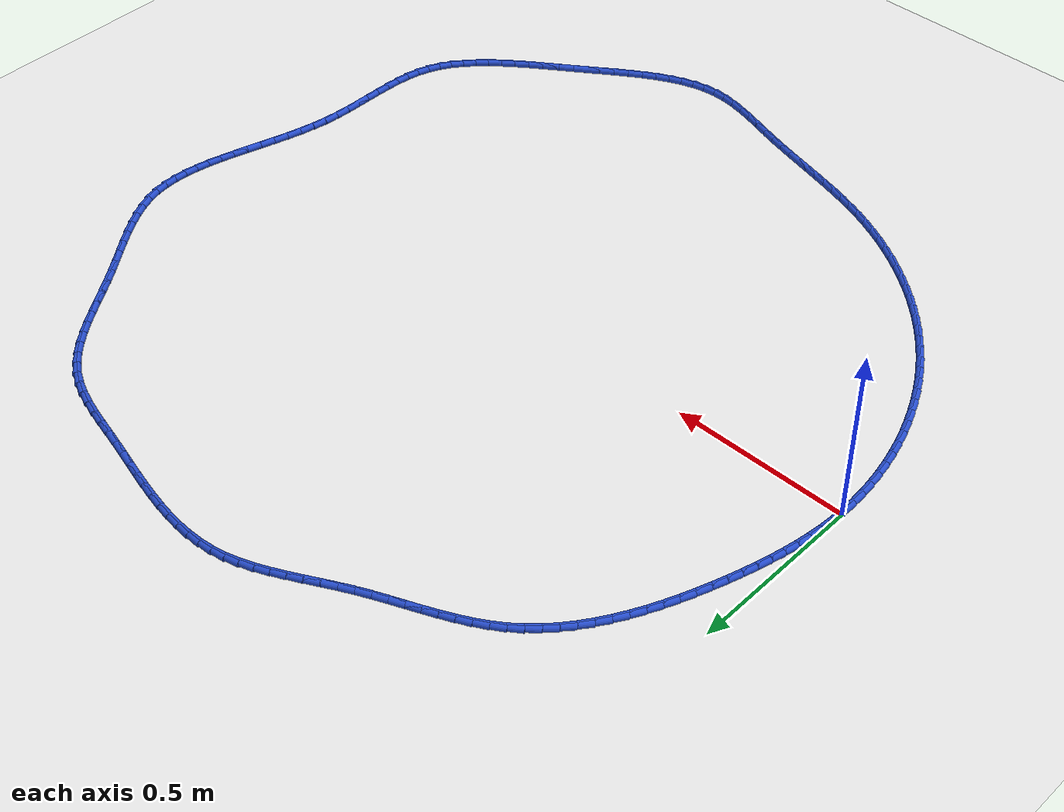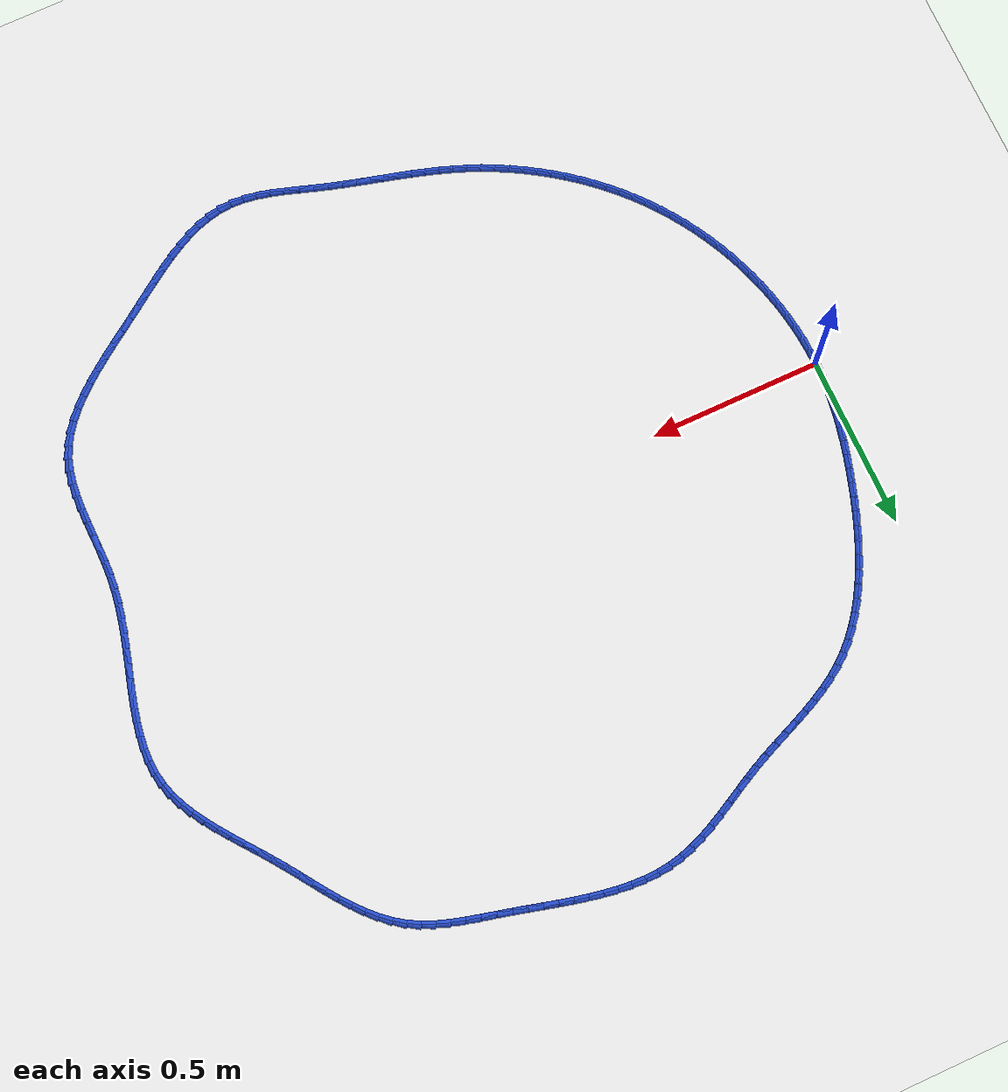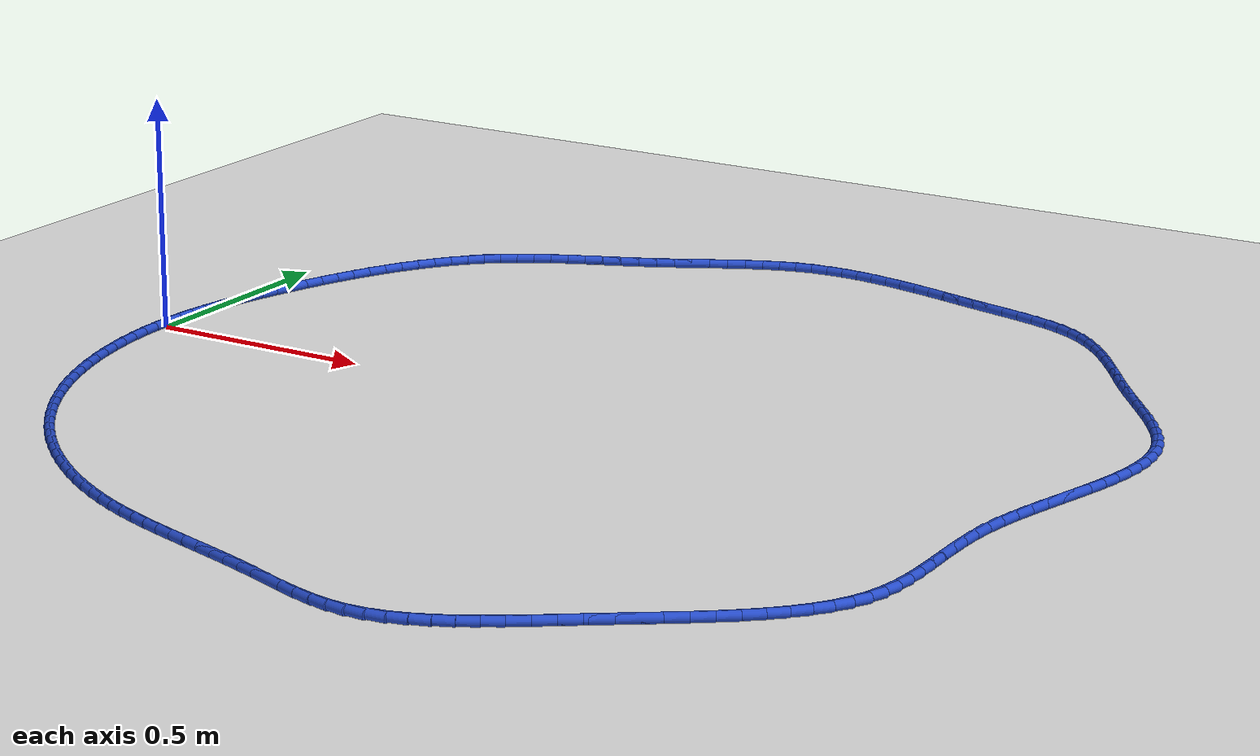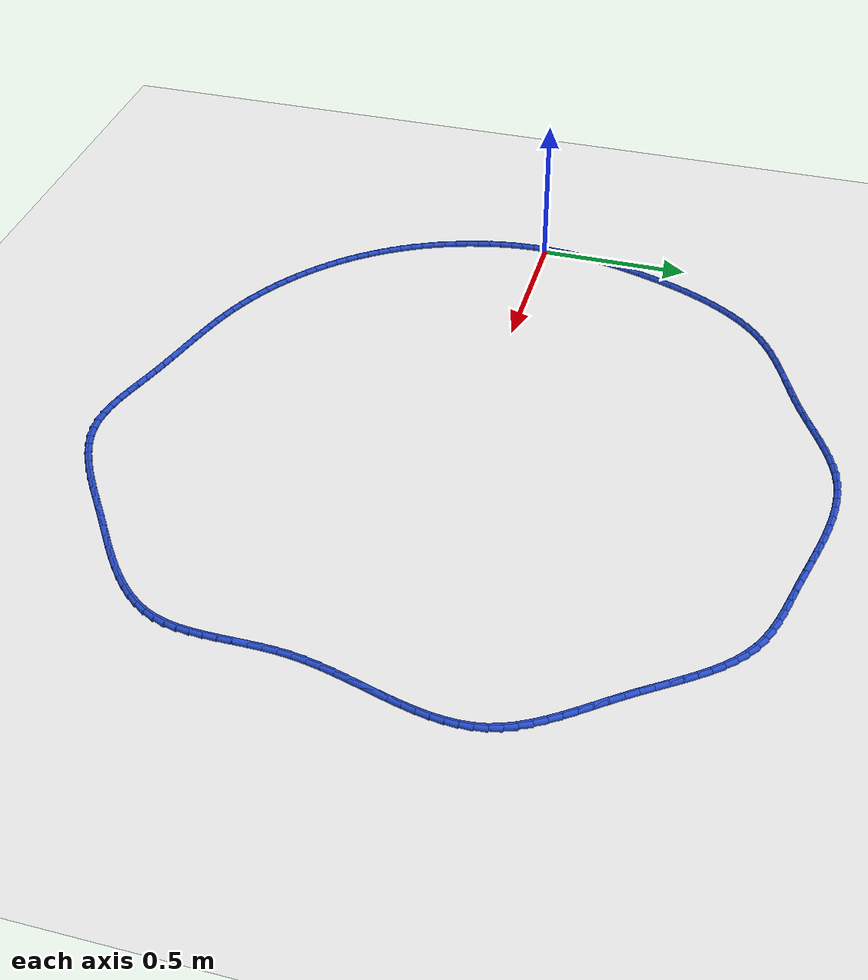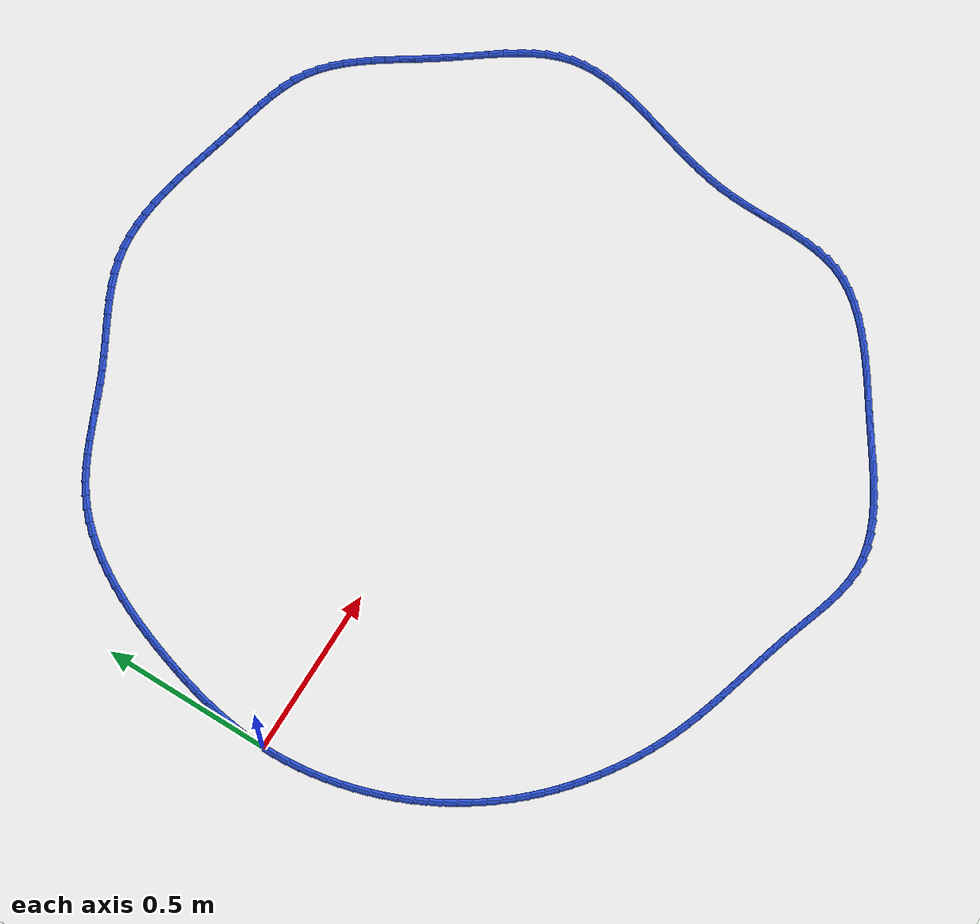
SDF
<sdf version="1.6">
 <world name="default">
  <light name="sun" type="directional">
   <pose>0 0 10 0 -0 0</pose>
   <diffuse>0.8 0.8 0.8 1</diffuse>
   <specular>0.2 0.2 0.2 1</specular>
   <attenuation>
    <range>1000</range>
    <constant>0.9</constant>
    <linear>0.01</linear>
    <quadratic>0.001</quadratic>
   </attenuation>
   <direction>-0.5 0.1 -0.9</direction>
  </light>
  <model name="ground_plane">
   <static>1</static>
   <link name="link">
    <collision name="collision">
     <geometry><plane><normal>0 0 1</normal><size>100 100</size></plane></geometry>
     <surface><friction><ode><mu>100</mu><mu2>50</mu2></ode></friction></surface>
    </collision>
    <visual name="visual">
     <cast_shadows>0</cast_shadows>
     <geometry><plane><normal>0 0 1</normal><size>100 100</size></plane></geometry>
     <material>
      <script><uri>file://media/materials/scripts/gazebo.material</uri><name>Gazebo/WhiteGlow</name></script>
     </material>
    </visual>
   </link>
  </model>
  <gravity>0 0 -9.8</gravity>
  <magnetic_field>6e-06 2.3e-05 -4.2e-05</magnetic_field>
  <atmosphere type="adiabatic"/>
  <physics name="default_physics" default="0" type="ode">
   <max_step_size>0.001</max_step_size>
   <real_time_factor>1</real_time_factor>
   <real_time_update_rate>1000</real_time_update_rate>
  </physics>
  <scene><ambient>0.4 0.4 0.4 1</ambient><background>0.7 0.7 0.7 1</background><shadows>1</shadows></scene>
  <spherical_coordinates>
   <surface_model>EARTH_WGS84</surface_model>
   <latitude_deg>0</latitude_deg>
   <longitude_deg>0</longitude_deg>
   <elevation>0</elevation>
   <heading_deg>0</heading_deg>
  </spherical_coordinates>
  <model name="line">
   <link name="link_0">
    <pose>-2.0816681711721685e-17 4.163336342344337e-17 0.01 0 1.57 1.536541923862688</pose>
    <collision name="collision">
     <geometry><cylinder><radius>0.01</radius><length>0.08</length></cylinder></geometry>
    </collision>
    <visual name="visual">
     <material>
      <script><name>Gazebo/Blue</name><uri>file://media/materials/scripts/gazebo.material</uri></script>
     </material>
     <geometry><cylinder><radius>0.01</radius><length>0.08</length></cylinder></geometry>
    </visual>
   </link>
   <link name="link_1">
    <pose>0.0013572058669911254 0.03960585726526232 0.01 0 1.57 1.4931692959205023</pose>
    <collision name="collision">
     <geometry><cylinder><radius>0.01</radius><length>0.08</length></cylinder></geometry>
    </collision>
    <visual name="visual">
     <material>
      <script><name>Gazebo/Blue</name><uri>file://media/materials/scripts/gazebo.material</uri></script>
     </material>
     <geometry><cylinder><radius>0.01</radius><length>0.08</length></cylinder></geometry>
    </visual>
   </link>
   <link name="link_2">
    <pose>0.004425729709717585 0.07905548884631912 0.01 0 1.57 1.4524673663735053</pose>
    <collision name="collision">
     <geometry><cylinder><radius>0.01</radius><length>0.08</length></cylinder></geometry>
    </collision>
    <visual name="visual">
     <material>
      <script><name>Gazebo/Blue</name><uri>file://media/materials/scripts/gazebo.material</uri></script>
     </material>
     <geometry><cylinder><radius>0.01</radius><length>0.08</length></cylinder></geometry>
    </visual>
   </link>
   <link name="link_3">
    <pose>0.00910084058042875 0.11838035537991416 0.01 0 1.57 1.4146294556732217</pose>
    <collision name="collision">
     <geometry><cylinder><radius>0.01</radius><length>0.08</length></cylinder></geometry>
    </collision>
    <visual name="visual">
     <material>
      <script><name>Gazebo/Blue</name><uri>file://media/materials/scripts/gazebo.material</uri></script>
     </material>
     <geometry><cylinder><radius>0.01</radius><length>0.08</length></cylinder></geometry>
    </visual>
   </link>
   <link name="link_4">
    <pose>0.015277807531374013 0.1576119175027912 0.01 0 1.57 1.3797876665798456</pose>
    <collision name="collision">
     <geometry><cylinder><radius>0.01</radius><length>0.08</length></cylinder></geometry>
    </collision>
    <visual name="visual">
     <material>
      <script><name>Gazebo/Blue</name><uri>file://media/materials/scripts/gazebo.material</uri></script>
     </material>
     <geometry><cylinder><radius>0.01</radius><length>0.08</length></cylinder></geometry>
    </visual>
   </link>
   <link name="link_5">
    <pose>0.022851899614802784 0.19678163585169395 0.01 0 1.57 1.3480199460998947</pose>
    <collision name="collision">
     <geometry><cylinder><radius>0.01</radius><length>0.08</length></cylinder></geometry>
    </collision>
    <visual name="visual">
     <material>
      <script><name>Gazebo/Blue</name><uri>file://media/materials/scripts/gazebo.material</uri></script>
     </material>
     <geometry><cylinder><radius>0.01</radius><length>0.08</length></cylinder></geometry>
    </visual>
   </link>
   <link name="link_6">
    <pose>0.03171838588296445 0.23592097106336612 0.01 0 1.57 1.3193586703346116</pose>
    <collision name="collision">
     <geometry><cylinder><radius>0.01</radius><length>0.08</length></cylinder></geometry>
    </collision>
    <visual name="visual">
     <material>
      <script><name>Gazebo/Blue</name><uri>file://media/materials/scripts/gazebo.material</uri></script>
     </material>
     <geometry><cylinder><radius>0.01</radius><length>0.08</length></cylinder></geometry>
    </visual>
   </link>
   <link name="link_7">
    <pose>0.04177253538810839 0.27506138377455147 0.01 0 1.57 1.2937996988057787</pose>
    <collision name="collision">
     <geometry><cylinder><radius>0.01</radius><length>0.08</length></cylinder></geometry>
    </collision>
    <visual name="visual">
     <material>
      <script><name>Gazebo/Blue</name><uri>file://media/materials/scripts/gazebo.material</uri></script>
     </material>
     <geometry><cylinder><radius>0.01</radius><length>0.08</length></cylinder></geometry>
    </visual>
   </link>
   <link name="link_8">
    <pose>0.05290961718248402 0.3142343346219937 0.01 0 1.57 1.2713111083744824</pose>
    <collision name="collision">
     <geometry><cylinder><radius>0.01</radius><length>0.08</length></cylinder></geometry>
    </collision>
    <visual name="visual">
     <material>
      <script><name>Gazebo/Blue</name><uri>file://media/materials/scripts/gazebo.material</uri></script>
     </material>
     <geometry><cylinder><radius>0.01</radius><length>0.08</length></cylinder></geometry>
    </visual>
   </link>
   <link name="link_9">
    <pose>0.06502490031834073 0.3534712842424365 0.01 0 1.57 1.251303823343375</pose>
    <collision name="collision">
     <geometry><cylinder><radius>0.01</radius><length>0.08</length></cylinder></geometry>
    </collision>
    <visual name="visual">
     <material>
      <script><name>Gazebo/Blue</name><uri>file://media/materials/scripts/gazebo.material</uri></script>
     </material>
     <geometry><cylinder><radius>0.01</radius><length>0.08</length></cylinder></geometry>
    </visual>
   </link>
   <link name="link_10">
    <pose>0.07803020135055229 0.39278285707645455 0.01 0 1.57 1.2297427222754966</pose>
    <collision name="collision">
     <geometry><cylinder><radius>0.01</radius><length>0.08</length></cylinder></geometry>
    </collision>
    <visual name="visual">
     <material>
      <script><name>Gazebo/Blue</name><uri>file://media/materials/scripts/gazebo.material</uri></script>
     </material>
     <geometry><cylinder><radius>0.01</radius><length>0.08</length></cylinder></geometry>
    </visual>
   </link>
   <link name="link_11">
    <pose>0.09195876311424779 0.43202678066815897 0.01 0 1.57 1.2046900887845857</pose>
    <collision name="collision">
     <geometry><cylinder><radius>0.01</radius><length>0.08</length></cylinder></geometry>
    </collision>
    <visual name="visual">
     <material>
      <script><name>Gazebo/Blue</name><uri>file://media/materials/scripts/gazebo.material</uri></script>
     </material>
     <geometry><cylinder><radius>0.01</radius><length>0.08</length></cylinder></geometry>
    </visual>
   </link>
   <link name="link_12">
    <pose>0.10689791344220063 0.4709926801025592 0.01 0 1.57 1.1758911015616755</pose>
    <collision name="collision">
     <geometry><cylinder><radius>0.01</radius><length>0.08</length></cylinder></geometry>
    </collision>
    <visual name="visual">
     <material>
      <script><name>Gazebo/Blue</name><uri>file://media/materials/scripts/gazebo.material</uri></script>
     </material>
     <geometry><cylinder><radius>0.01</radius><length>0.08</length></cylinder></geometry>
    </visual>
   </link>
   <link name="link_13">
    <pose>0.12293522811182156 0.5094698682590566 0.01 0 1.57 1.1430432878604047</pose>
    <collision name="collision">
     <geometry><cylinder><radius>0.01</radius><length>0.08</length></cylinder></geometry>
    </collision>
    <visual name="visual">
     <material>
      <script><name>Gazebo/Blue</name><uri>file://media/materials/scripts/gazebo.material</uri></script>
     </material>
     <geometry><cylinder><radius>0.01</radius><length>0.08</length></cylinder></geometry>
    </visual>
   </link>
   <link name="link_14">
    <pose>0.1401582829005215 0.547247658017053 0.01 0 1.57 1.1057930347961435</pose>
    <collision name="collision">
     <geometry><cylinder><radius>0.01</radius><length>0.08</length></cylinder></geometry>
    </collision>
    <visual name="visual">
     <material>
      <script><name>Gazebo/Blue</name><uri>file://media/materials/scripts/gazebo.material</uri></script>
     </material>
     <geometry><cylinder><radius>0.01</radius><length>0.08</length></cylinder></geometry>
    </visual>
   </link>
   <link name="link_15">
    <pose>0.15865465358571135 0.5841153622559501 0.01 0 1.57 1.063743657000141</pose>
    <collision name="collision">
     <geometry><cylinder><radius>0.01</radius><length>0.08</length></cylinder></geometry>
    </collision>
    <visual name="visual">
     <material>
      <script><name>Gazebo/Blue</name><uri>file://media/materials/scripts/gazebo.material</uri></script>
     </material>
     <geometry><cylinder><radius>0.01</radius><length>0.08</length></cylinder></geometry>
    </visual>
   </link>
   <link name="link_16">
    <pose>0.178511915944802 0.6198622938551496 0.01 0 1.57 1.0164696327096898</pose>
    <collision name="collision">
     <geometry><cylinder><radius>0.01</radius><length>0.08</length></cylinder></geometry>
    </collision>
    <visual name="visual">
     <material>
      <script><name>Gazebo/Blue</name><uri>file://media/materials/scripts/gazebo.material</uri></script>
     </material>
     <geometry><cylinder><radius>0.01</radius><length>0.08</length></cylinder></geometry>
    </visual>
   </link>
   <link name="link_17">
    <pose>0.1998176457552043 0.6542777656940533 0.01 0 1.57 0.9635403756393454</pose>
    <collision name="collision">
     <geometry><cylinder><radius>0.01</radius><length>0.08</length></cylinder></geometry>
    </collision>
    <visual name="visual">
     <material>
      <script><name>Gazebo/Blue</name><uri>file://media/materials/scripts/gazebo.material</uri></script>
     </material>
     <geometry><cylinder><radius>0.01</radius><length>0.08</length></cylinder></geometry>
    </visual>
   </link>
   <link name="link_18">
    <pose>0.222659418794329 0.6871510906520626 0.01 0 1.57 0.9045573867498293</pose>
    <collision name="collision">
     <geometry><cylinder><radius>0.01</radius><length>0.08</length></cylinder></geometry>
    </collision>
    <visual name="visual">
     <material>
      <script><name>Gazebo/Blue</name><uri>file://media/materials/scripts/gazebo.material</uri></script>
     </material>
     <geometry><cylinder><radius>0.01</radius><length>0.08</length></cylinder></geometry>
    </visual>
   </link>
   <link name="link_19">
    <pose>0.24712481083958712 0.7182715816085796 0.01 0 1.57 0.8392082929744844</pose>
    <collision name="collision">
     <geometry><cylinder><radius>0.01</radius><length>0.08</length></cylinder></geometry>
    </collision>
    <visual name="visual">
     <material>
      <script><name>Gazebo/Blue</name><uri>file://media/materials/scripts/gazebo.material</uri></script>
     </material>
     <geometry><cylinder><radius>0.01</radius><length>0.08</length></cylinder></geometry>
    </visual>
   </link>
   <link name="link_20">
    <pose>0.27330139766838957 0.7474285514430061 0.01 0 1.57 0.7673391775736776</pose>
    <collision name="collision">
     <geometry><cylinder><radius>0.01</radius><length>0.08</length></cylinder></geometry>
    </collision>
    <visual name="visual">
     <material>
      <script><name>Gazebo/Blue</name><uri>file://media/materials/scripts/gazebo.material</uri></script>
     </material>
     <geometry><cylinder><radius>0.01</radius><length>0.08</length></cylinder></geometry>
    </visual>
   </link>
   <link name="link_21">
    <pose>0.3012767550581471 0.7744113130347433 0.01 0 1.57 0.6890478365013732</pose>
    <collision name="collision">
     <geometry><cylinder><radius>0.01</radius><length>0.08</length></cylinder></geometry>
    </collision>
    <visual name="visual">
     <material>
      <script><name>Gazebo/Blue</name><uri>file://media/materials/scripts/gazebo.material</uri></script>
     </material>
     <geometry><cylinder><radius>0.01</radius><length>0.08</length></cylinder></geometry>
    </visual>
   </link>
   <link name="link_22">
    <pose>0.331138337856369 0.7990093918339223 0.01 0 1.57 0.6092066559635796</pose>
    <collision name="collision">
     <geometry><cylinder><radius>0.01</radius><length>0.08</length></cylinder></geometry>
    </collision>
    <visual name="visual">
     <material>
      <script><name>Gazebo/Blue</name><uri>file://media/materials/scripts/gazebo.material</uri></script>
     </material>
     <geometry><cylinder><radius>0.01</radius><length>0.08</length></cylinder></geometry>
    </visual>
   </link>
   <link name="link_23">
    <pose>0.36288817306078736 0.8211624784698073 0.01 0 1.57 0.5408208876783689</pose>
    <collision name="collision">
     <geometry><cylinder><radius>0.01</radius><length>0.08</length></cylinder></geometry>
    </collision>
    <visual name="visual">
     <material>
      <script><name>Gazebo/Blue</name><uri>file://media/materials/scripts/gazebo.material</uri></script>
     </material>
     <geometry><cylinder><radius>0.01</radius><length>0.08</length></cylinder></geometry>
    </visual>
   </link>
   <link name="link_24">
    <pose>0.3962931010205366 0.841223674951069 0.01 0 1.57 0.48636983674301204</pose>
    <collision name="collision">
     <geometry><cylinder><radius>0.01</radius><length>0.08</length></cylinder></geometry>
    </collision>
    <visual name="visual">
     <material>
      <script><name>Gazebo/Blue</name><uri>file://media/materials/scripts/gazebo.material</uri></script>
     </material>
     <geometry><cylinder><radius>0.01</radius><length>0.08</length></cylinder></geometry>
    </visual>
   </link>
   <link name="link_25">
    <pose>0.4310798386859627 0.8596166122459875 0.01 0 1.57 0.4456748754470123</pose>
    <collision name="collision">
     <geometry><cylinder><radius>0.01</radius><length>0.08</length></cylinder></geometry>
    </collision>
    <visual name="visual">
     <material>
      <script><name>Gazebo/Blue</name><uri>file://media/materials/scripts/gazebo.material</uri></script>
     </material>
     <geometry><cylinder><radius>0.01</radius><length>0.08</length></cylinder></geometry>
    </visual>
   </link>
   <link name="link_26">
    <pose>0.466975103007412 0.8767649213228433 0.01 0 1.57 0.4182843844014696</pose>
    <collision name="collision">
     <geometry><cylinder><radius>0.01</radius><length>0.08</length></cylinder></geometry>
    </collision>
    <visual name="visual">
     <material>
      <script><name>Gazebo/Blue</name><uri>file://media/materials/scripts/gazebo.material</uri></script>
     </material>
     <geometry><cylinder><radius>0.01</radius><length>0.08</length></cylinder></geometry>
    </visual>
   </link>
   <link name="link_27">
    <pose>0.5037056109352306 0.8930922331499167 0.01 0 1.57 0.4037009110901891</pose>
    <collision name="collision">
     <geometry><cylinder><radius>0.01</radius><length>0.08</length></cylinder></geometry>
    </collision>
    <visual name="visual">
     <material>
      <script><name>Gazebo/Blue</name><uri>file://media/materials/scripts/gazebo.material</uri></script>
     </material>
     <geometry><cylinder><radius>0.01</radius><length>0.08</length></cylinder></geometry>
    </visual>
   </link>
   <link name="link_28">
    <pose>0.5409980794197649 0.909022178695488 0.01 0 1.57 0.40151501372175835</pose>
    <collision name="collision">
     <geometry><cylinder><radius>0.01</radius><length>0.08</length></cylinder></geometry>
    </collision>
    <visual name="visual">
     <material>
      <script><name>Gazebo/Blue</name><uri>file://media/materials/scripts/gazebo.material</uri></script>
     </material>
     <geometry><cylinder><radius>0.01</radius><length>0.08</length></cylinder></geometry>
    </visual>
   </link>
   <link name="link_29">
    <pose>0.5785792254113608 0.9249783889278371 0.01 0 1.57 0.41146390240227254</pose>
    <collision name="collision">
     <geometry><cylinder><radius>0.01</radius><length>0.08</length></cylinder></geometry>
    </collision>
    <visual name="visual">
     <material>
      <script><name>Gazebo/Blue</name><uri>file://media/materials/scripts/gazebo.material</uri></script>
     </material>
     <geometry><cylinder><radius>0.01</radius><length>0.08</length></cylinder></geometry>
    </visual>
   </link>
   <link name="link_30">
    <pose>0.6161757658603645 0.9413844948152443 0.01 0 1.57 0.4334319336008633</pose>
    <collision name="collision">
     <geometry><cylinder><radius>0.01</radius><length>0.08</length></cylinder></geometry>
    </collision>
    <visual name="visual">
     <material>
      <script><name>Gazebo/Blue</name><uri>file://media/materials/scripts/gazebo.material</uri></script>
     </material>
     <geometry><cylinder><radius>0.01</radius><length>0.08</length></cylinder></geometry>
    </visual>
   </link>
   <link name="link_31">
    <pose>0.6535144177171223 0.95866412732599 0.01 0 1.57 0.4639782111188147</pose>
    <collision name="collision">
     <geometry><cylinder><radius>0.01</radius><length>0.08</length></cylinder></geometry>
    </collision>
    <visual name="visual">
     <material>
      <script><name>Gazebo/Blue</name><uri>file://media/materials/scripts/gazebo.material</uri></script>
     </material>
     <geometry><cylinder><radius>0.01</radius><length>0.08</length></cylinder></geometry>
    </visual>
   </link>
   <link name="link_32">
    <pose>0.6903745470027037 0.977109427033723 0.01 0 1.57 0.4855326255182563</pose>
    <collision name="collision">
     <geometry><cylinder><radius>0.01</radius><length>0.08</length></cylinder></geometry>
    </collision>
    <visual name="visual">
     <material>
      <script><name>Gazebo/Blue</name><uri>file://media/materials/scripts/gazebo.material</uri></script>
     </material>
     <geometry><cylinder><radius>0.01</radius><length>0.08</length></cylinder></geometry>
    </visual>
   </link>
   <link name="link_33">
    <pose>0.7268073362203776 0.9963336762526644 0.01 0 1.57 0.4925641272505168</pose>
    <collision name="collision">
     <geometry><cylinder><radius>0.01</radius><length>0.08</length></cylinder></geometry>
    </collision>
    <visual name="visual">
     <material>
      <script><name>Gazebo/Blue</name><uri>file://media/materials/scripts/gazebo.material</uri></script>
     </material>
     <geometry><cylinder><radius>0.01</radius><length>0.08</length></cylinder></geometry>
    </visual>
   </link>
   <link name="link_34">
    <pose>0.7629514318961249 1.0157317169959141 0.01 0 1.57 0.4849632190556711</pose>
    <collision name="collision">
     <geometry><cylinder><radius>0.01</radius><length>0.08</length></cylinder></geometry>
    </collision>
    <visual name="visual">
     <material>
      <script><name>Gazebo/Blue</name><uri>file://media/materials/scripts/gazebo.material</uri></script>
     </material>
     <geometry><cylinder><radius>0.01</radius><length>0.08</length></cylinder></geometry>
    </visual>
   </link>
   <link name="link_35">
    <pose>0.7989455222939997 1.0346982870362573 0.01 0 1.57 0.4622782496259544</pose>
    <collision name="collision">
     <geometry><cylinder><radius>0.01</radius><length>0.08</length></cylinder></geometry>
    </collision>
    <visual name="visual">
     <material>
      <script><name>Gazebo/Blue</name><uri>file://media/materials/scripts/gazebo.material</uri></script>
     </material>
     <geometry><cylinder><radius>0.01</radius><length>0.08</length></cylinder></geometry>
    </visual>
   </link>
   <link name="link_36">
    <pose>0.834928295678057 1.0526281241464797 0.01 0 1.57 0.42373507588505827</pose>
    <collision name="collision">
     <geometry><cylinder><radius>0.01</radius><length>0.08</length></cylinder></geometry>
    </collision>
    <visual name="visual">
     <material>
      <script><name>Gazebo/Blue</name><uri>file://media/materials/scripts/gazebo.material</uri></script>
     </material>
     <geometry><cylinder><radius>0.01</radius><length>0.08</length></cylinder></geometry>
    </visual>
   </link>
   <link name="link_37">
    <pose>0.8710384403123508 1.0689159660993663 0.01 0 1.57 0.3683643806551028</pose>
    <collision name="collision">
     <geometry><cylinder><radius>0.01</radius><length>0.08</length></cylinder></geometry>
    </collision>
    <visual name="visual">
     <material>
      <script><name>Gazebo/Blue</name><uri>file://media/materials/scripts/gazebo.material</uri></script>
     </material>
     <geometry><cylinder><radius>0.01</radius><length>0.08</length></cylinder></geometry>
    </visual>
   </link>
   <link name="link_38">
    <pose>0.9074146444609351 1.0829565506677024 0.01 0 1.57 0.2952881023247882</pose>
    <collision name="collision">
     <geometry><cylinder><radius>0.01</radius><length>0.08</length></cylinder></geometry>
    </collision>
    <visual name="visual">
     <material>
      <script><name>Gazebo/Blue</name><uri>file://media/materials/scripts/gazebo.material</uri></script>
     </material>
     <geometry><cylinder><radius>0.01</radius><length>0.08</length></cylinder></geometry>
    </visual>
   </link>
   <link name="link_39">
    <pose>0.9441955963878651 1.0941446156242733 0.01 0 1.57 0.20523916451723268</pose>
    <collision name="collision">
     <geometry><cylinder><radius>0.01</radius><length>0.08</length></cylinder></geometry>
    </collision>
    <visual name="visual">
     <material>
      <script><name>Gazebo/Blue</name><uri>file://media/materials/scripts/gazebo.material</uri></script>
     </material>
     <geometry><cylinder><radius>0.01</radius><length>0.08</length></cylinder></geometry>
    </visual>
   </link>
   <link name="link_40">
    <pose>0.9815124953438802 1.1019128869206494 0.01 0 1.57 0.11330357779717276</pose>
    <collision name="collision">
     <geometry><cylinder><radius>0.01</radius><length>0.08</length></cylinder></geometry>
    </collision>
    <visual name="visual">
     <material>
      <script><name>Gazebo/Blue</name><uri>file://media/materials/scripts/gazebo.material</uri></script>
     </material>
     <geometry><cylinder><radius>0.01</radius><length>0.08</length></cylinder></geometry>
    </visual>
   </link>
   <link name="link_41">
    <pose>1.0193922205260058 1.1062232561921732 0.01 0 1.57 0.03131134509089555</pose>
    <collision name="collision">
     <geometry><cylinder><radius>0.01</radius><length>0.08</length></cylinder></geometry>
    </collision>
    <visual name="visual">
     <material>
      <script><name>Gazebo/Blue</name><uri>file://media/materials/scripts/gazebo.material</uri></script>
     </material>
     <geometry><cylinder><radius>0.01</radius><length>0.08</length></cylinder></geometry>
    </visual>
   </link>
   <link name="link_42">
    <pose>1.0577851275103651 1.1074257827633074 0.01 0 1.57 -0.039776522073871674</pose>
    <collision name="collision">
     <geometry><cylinder><radius>0.01</radius><length>0.08</length></cylinder></geometry>
    </collision>
    <visual name="visual">
     <material>
      <script><name>Gazebo/Blue</name><uri>file://media/materials/scripts/gazebo.material</uri></script>
     </material>
     <geometry><cylinder><radius>0.01</radius><length>0.08</length></cylinder></geometry>
    </visual>
   </link>
   <link name="link_43">
    <pose>1.0966398100139014 1.1058794630265538 0.01 0 1.57 -0.09991234392856023</pose>
    <collision name="collision">
     <geometry><cylinder><radius>0.01</radius><length>0.08</length></cylinder></geometry>
    </collision>
    <visual name="visual">
     <material>
      <script><name>Gazebo/Blue</name><uri>file://media/materials/scripts/gazebo.material</uri></script>
     </material>
     <geometry><cylinder><radius>0.01</radius><length>0.08</length></cylinder></geometry>
    </visual>
   </link>
   <link name="link_44">
    <pose>1.1359048617535579 1.1019432933744149 0.01 0 1.57 -0.1494679709837708</pose>
    <collision name="collision">
     <geometry><cylinder><radius>0.01</radius><length>0.08</length></cylinder></geometry>
    </collision>
    <visual name="visual">
     <material>
      <script><name>Gazebo/Blue</name><uri>file://media/materials/scripts/gazebo.material</uri></script>
     </material>
     <geometry><cylinder><radius>0.01</radius><length>0.08</length></cylinder></geometry>
    </visual>
   </link>
   <link name="link_45">
    <pose>1.1755288764462786 1.095976270199393 0.01 0 1.57 -0.18901564419574585</pose>
    <collision name="collision">
     <geometry><cylinder><radius>0.01</radius><length>0.08</length></cylinder></geometry>
    </collision>
    <visual name="visual">
     <material>
      <script><name>Gazebo/Blue</name><uri>file://media/materials/scripts/gazebo.material</uri></script>
     </material>
     <geometry><cylinder><radius>0.01</radius><length>0.08</length></cylinder></geometry>
    </visual>
   </link>
   <link name="link_46">
    <pose>1.2154604478090048 1.0883373898939896 0.01 0 1.57 -0.2191700770469787</pose>
    <collision name="collision">
     <geometry><cylinder><radius>0.01</radius><length>0.08</length></cylinder></geometry>
    </collision>
    <visual name="visual">
     <material>
      <script><name>Gazebo/Blue</name><uri>file://media/materials/scripts/gazebo.material</uri></script>
     </material>
     <geometry><cylinder><radius>0.01</radius><length>0.08</length></cylinder></geometry>
    </visual>
   </link>
   <link name="link_47">
    <pose>1.2556481695586816 1.0793856488507079 0.01 0 1.57 -0.24048799674733226</pose>
    <collision name="collision">
     <geometry><cylinder><radius>0.01</radius><length>0.08</length></cylinder></geometry>
    </collision>
    <visual name="visual">
     <material>
      <script><name>Gazebo/Blue</name><uri>file://media/materials/scripts/gazebo.material</uri></script>
     </material>
     <geometry><cylinder><radius>0.01</radius><length>0.08</length></cylinder></geometry>
    </visual>
   </link>
   <link name="link_48">
    <pose>1.2960406354122502 1.0694800434620493 0.01 0 1.57 -0.25341058394167215</pose>
    <collision name="collision">
     <geometry><cylinder><radius>0.01</radius><length>0.08</length></cylinder></geometry>
    </collision>
    <visual name="visual">
     <material>
      <script><name>Gazebo/Blue</name><uri>file://media/materials/scripts/gazebo.material</uri></script>
     </material>
     <geometry><cylinder><radius>0.01</radius><length>0.08</length></cylinder></geometry>
    </visual>
   </link>
   <link name="link_49">
    <pose>1.3365864390866549 1.058979570120516 0.01 0 1.57 -0.25823398998272024</pose>
    <collision name="collision">
     <geometry><cylinder><radius>0.01</radius><length>0.08</length></cylinder></geometry>
    </collision>
    <visual name="visual">
     <material>
      <script><name>Gazebo/Blue</name><uri>file://media/materials/scripts/gazebo.material</uri></script>
     </material>
     <geometry><cylinder><radius>0.01</radius><length>0.08</length></cylinder></geometry>
    </visual>
   </link>
   <link name="link_50">
    <pose>1.377234174298839 1.0482432252186102 0.01 0 1.57 -0.2550968671294141</pose>
    <collision name="collision">
     <geometry><cylinder><radius>0.01</radius><length>0.08</length></cylinder></geometry>
    </collision>
    <visual name="visual">
     <material>
      <script><name>Gazebo/Blue</name><uri>file://media/materials/scripts/gazebo.material</uri></script>
     </material>
     <geometry><cylinder><radius>0.01</radius><length>0.08</length></cylinder></geometry>
    </visual>
   </link>
   <link name="link_51">
    <pose>1.4179324347657447 1.0376300051488345 0.01 0 1.57 -0.2447363298845203</pose>
    <collision name="collision">
     <geometry><cylinder><radius>0.01</radius><length>0.08</length></cylinder></geometry>
    </collision>
    <visual name="visual">
     <material>
      <script><name>Gazebo/Blue</name><uri>file://media/materials/scripts/gazebo.material</uri></script>
     </material>
     <geometry><cylinder><radius>0.01</radius><length>0.08</length></cylinder></geometry>
    </visual>
   </link>
   <link name="link_52">
    <pose>1.4586198008028184 1.0274686391502976 0.01 0 1.57 -0.24012418256702928</pose>
    <collision name="collision">
     <geometry><cylinder><radius>0.01</radius><length>0.08</length></cylinder></geometry>
    </collision>
    <visual name="visual">
     <material>
      <script><name>Gazebo/Blue</name><uri>file://media/materials/scripts/gazebo.material</uri></script>
     </material>
     <geometry><cylinder><radius>0.01</radius><length>0.08</length></cylinder></geometry>
    </visual>
   </link>
   <link name="link_53">
    <pose>1.4990623224808628 1.0175663554136716 0.01 0 1.57 -0.2525546629126688</pose>
    <collision name="collision">
     <geometry><cylinder><radius>0.01</radius><length>0.08</length></cylinder></geometry>
    </collision>
    <visual name="visual">
     <material>
      <script><name>Gazebo/Blue</name><uri>file://media/materials/scripts/gazebo.material</uri></script>
     </material>
     <geometry><cylinder><radius>0.01</radius><length>0.08</length></cylinder></geometry>
    </visual>
   </link>
   <link name="link_54">
    <pose>1.538880575153186 1.0072906608630607 0.01 0 1.57 -0.28321875968008486</pose>
    <collision name="collision">
     <geometry><cylinder><radius>0.01</radius><length>0.08</length></cylinder></geometry>
    </collision>
    <visual name="visual">
     <material>
      <script><name>Gazebo/Blue</name><uri>file://media/materials/scripts/gazebo.material</uri></script>
     </material>
     <geometry><cylinder><radius>0.01</radius><length>0.08</length></cylinder></geometry>
    </visual>
   </link>
   <link name="link_55">
    <pose>1.5776905812762383 0.9959953005427917 0.01 0 1.57 -0.3334584047757404</pose>
    <collision name="collision">
     <geometry><cylinder><radius>0.01</radius><length>0.08</length></cylinder></geometry>
    </collision>
    <visual name="visual">
     <material>
      <script><name>Gazebo/Blue</name><uri>file://media/materials/scripts/gazebo.material</uri></script>
     </material>
     <geometry><cylinder><radius>0.01</radius><length>0.08</length></cylinder></geometry>
    </visual>
   </link>
   <link name="link_56">
    <pose>1.6151083633064696 0.9830340194971919 0.01 0 1.57 -0.404856081282938</pose>
    <collision name="collision">
     <geometry><cylinder><radius>0.01</radius><length>0.08</length></cylinder></geometry>
    </collision>
    <visual name="visual">
     <material>
      <script><name>Gazebo/Blue</name><uri>file://media/materials/scripts/gazebo.material</uri></script>
     </material>
     <geometry><cylinder><radius>0.01</radius><length>0.08</length></cylinder></geometry>
    </visual>
   </link>
   <link name="link_57">
    <pose>1.6507499437003297 0.9677605627705878 0.01 0 1.57 -0.49863988104257734</pose>
    <collision name="collision">
     <geometry><cylinder><radius>0.01</radius><length>0.08</length></cylinder></geometry>
    </collision>
    <visual name="visual">
     <material>
      <script><name>Gazebo/Blue</name><uri>file://media/materials/scripts/gazebo.material</uri></script>
     </material>
     <geometry><cylinder><radius>0.01</radius><length>0.08</length></cylinder></geometry>
    </visual>
   </link>
   <link name="link_58">
    <pose>1.6842313450135862 0.9495286755501303 0.01 0 1.57 -0.6087094381813322</pose>
    <collision name="collision">
     <geometry><cylinder><radius>0.01</radius><length>0.08</length></cylinder></geometry>
    </collision>
    <visual name="visual">
     <material>
      <script><name>Gazebo/Blue</name><uri>file://media/materials/scripts/gazebo.material</uri></script>
     </material>
     <geometry><cylinder><radius>0.01</radius><length>0.08</length></cylinder></geometry>
    </visual>
   </link>
   <link name="link_59">
    <pose>1.7152966063489659 0.9278762006035781 0.01 0 1.57 -0.7097259664589791</pose>
    <collision name="collision">
     <geometry><cylinder><radius>0.01</radius><length>0.08</length></cylinder></geometry>
    </collision>
    <visual name="visual">
     <material>
      <script><name>Gazebo/Blue</name><uri>file://media/materials/scripts/gazebo.material</uri></script>
     </material>
     <geometry><cylinder><radius>0.01</radius><length>0.08</length></cylinder></geometry>
    </visual>
   </link>
   <link name="link_60">
    <pose>1.7441877843353424 0.903057167971652 0.01 0 1.57 -0.7941316065554348</pose>
    <collision name="collision">
     <geometry><cylinder><radius>0.01</radius><length>0.08</length></cylinder></geometry>
    </collision>
    <visual name="visual">
     <material>
      <script><name>Gazebo/Blue</name><uri>file://media/materials/scripts/gazebo.material</uri></script>
     </material>
     <geometry><cylinder><radius>0.01</radius><length>0.08</length></cylinder></geometry>
    </visual>
   </link>
   <link name="link_61">
    <pose>1.7712680236548386 0.8754997415720835 0.01 0 1.57 -0.8615605226695027</pose>
    <collision name="collision">
     <geometry><cylinder><radius>0.01</radius><length>0.08</length></cylinder></geometry>
    </collision>
    <visual name="visual">
     <material>
      <script><name>Gazebo/Blue</name><uri>file://media/materials/scripts/gazebo.material</uri></script>
     </material>
     <geometry><cylinder><radius>0.01</radius><length>0.08</length></cylinder></geometry>
    </visual>
   </link>
   <link name="link_62">
    <pose>1.7969004689895802 0.8456320853226063 0.01 0 1.57 -0.9126332693376479</pose>
    <collision name="collision">
     <geometry><cylinder><radius>0.01</radius><length>0.08</length></cylinder></geometry>
    </collision>
    <visual name="visual">
     <material>
      <script><name>Gazebo/Blue</name><uri>file://media/materials/scripts/gazebo.material</uri></script>
     </material>
     <geometry><cylinder><radius>0.01</radius><length>0.08</length></cylinder></geometry>
    </visual>
   </link>
   <link name="link_63">
    <pose>1.8214482650216912 0.8138823631409514 0.01 0 1.57 -0.948368195337595</pose>
    <collision name="collision">
     <geometry><cylinder><radius>0.01</radius><length>0.08</length></cylinder></geometry>
    </collision>
    <visual name="visual">
     <material>
      <script><name>Gazebo/Blue</name><uri>file://media/materials/scripts/gazebo.material</uri></script>
     </material>
     <geometry><cylinder><radius>0.01</radius><length>0.08</length></cylinder></geometry>
    </visual>
   </link>
   <link name="link_64">
    <pose>1.8452745564332957 0.7806787389448524 0.01 0 1.57 -0.9697947329129846</pose>
    <collision name="collision">
     <geometry><cylinder><radius>0.01</radius><length>0.08</length></cylinder></geometry>
    </collision>
    <visual name="visual">
     <material>
      <script><name>Gazebo/Blue</name><uri>file://media/materials/scripts/gazebo.material</uri></script>
     </material>
     <geometry><cylinder><radius>0.01</radius><length>0.08</length></cylinder></geometry>
    </visual>
   </link>
   <link name="link_65">
    <pose>1.8687424879065175 0.7464493766520407 0.01 0 1.57 -0.9777465847306135</pose>
    <collision name="collision">
     <geometry><cylinder><radius>0.01</radius><length>0.08</length></cylinder></geometry>
    </collision>
    <visual name="visual">
     <material>
      <script><name>Gazebo/Blue</name><uri>file://media/materials/scripts/gazebo.material</uri></script>
     </material>
     <geometry><cylinder><radius>0.01</radius><length>0.08</length></cylinder></geometry>
    </visual>
   </link>
   <link name="link_66">
    <pose>1.892215204123482 0.7116224401802488 0.01 0 1.57 -0.9727774201052961</pose>
    <collision name="collision">
     <geometry><cylinder><radius>0.01</radius><length>0.08</length></cylinder></geometry>
    </collision>
    <visual name="visual">
     <material>
      <script><name>Gazebo/Blue</name><uri>file://media/materials/scripts/gazebo.material</uri></script>
     </material>
     <geometry><cylinder><radius>0.01</radius><length>0.08</length></cylinder></geometry>
    </visual>
   </link>
   <link name="link_67">
    <pose>1.9160558497663136 0.6766260934472094 0.01 0 1.57 -0.9553386856616382</pose>
    <collision name="collision">
     <geometry><cylinder><radius>0.01</radius><length>0.08</length></cylinder></geometry>
    </collision>
    <visual name="visual">
     <material>
      <script><name>Gazebo/Blue</name><uri>file://media/materials/scripts/gazebo.material</uri></script>
     </material>
     <geometry><cylinder><radius>0.01</radius><length>0.08</length></cylinder></geometry>
    </visual>
   </link>
   <link name="link_68">
    <pose>1.9406207567551048 0.6418844425134815 0.01 0 1.57 -0.9352434066777803</pose>
    <collision name="collision">
     <geometry><cylinder><radius>0.01</radius><length>0.08</length></cylinder></geometry>
    </collision>
    <visual name="visual">
     <material>
      <script><name>Gazebo/Blue</name><uri>file://media/materials/scripts/gazebo.material</uri></script>
     </material>
     <geometry><cylinder><radius>0.01</radius><length>0.08</length></cylinder></geometry>
    </visual>
   </link>
   <link name="link_69">
    <pose>1.96590575556142 0.6076068694580767 0.01 0 1.57 -0.926781792273071</pose>
    <collision name="collision">
     <geometry><cylinder><radius>0.01</radius><length>0.08</length></cylinder></geometry>
    </collision>
    <visual name="visual">
     <material>
      <script><name>Gazebo/Blue</name><uri>file://media/materials/scripts/gazebo.material</uri></script>
     </material>
     <geometry><cylinder><radius>0.01</radius><length>0.08</length></cylinder></geometry>
    </visual>
   </link>
   <link name="link_70">
    <pose>1.9913740141914584 0.573685488826542 0.01 0 1.57 -0.9311460830651228</pose>
    <collision name="collision">
     <geometry><cylinder><radius>0.01</radius><length>0.08</length></cylinder></geometry>
    </collision>
    <visual name="visual">
     <material>
      <script><name>Gazebo/Blue</name><uri>file://media/materials/scripts/gazebo.material</uri></script>
     </material>
     <geometry><cylinder><radius>0.01</radius><length>0.08</length></cylinder></geometry>
    </visual>
   </link>
   <link name="link_71">
    <pose>2.016445802128246 0.5399868636951142 0.01 0 1.57 -0.9487967753553909</pose>
    <collision name="collision">
     <geometry><cylinder><radius>0.01</radius><length>0.08</length></cylinder></geometry>
    </collision>
    <visual name="visual">
     <material>
      <script><name>Gazebo/Blue</name><uri>file://media/materials/scripts/gazebo.material</uri></script>
     </material>
     <geometry><cylinder><radius>0.01</radius><length>0.08</length></cylinder></geometry>
    </visual>
   </link>
   <link name="link_72">
    <pose>2.0405413888548076 0.5063775571400304 0.01 0 1.57 -0.9806565306600971</pose>
    <collision name="collision">
     <geometry><cylinder><radius>0.01</radius><length>0.08</length></cylinder></geometry>
    </collision>
    <visual name="visual">
     <material>
      <script><name>Gazebo/Blue</name><uri>file://media/materials/scripts/gazebo.material</uri></script>
     </material>
     <geometry><cylinder><radius>0.01</radius><length>0.08</length></cylinder></geometry>
    </visual>
   </link>
   <link name="link_73">
    <pose>2.06308104385417 0.4727241322375277 0.01 0 1.57 -1.0280890743204334</pose>
    <collision name="collision">
     <geometry><cylinder><radius>0.01</radius><length>0.08</length></cylinder></geometry>
    </collision>
    <visual name="visual">
     <material>
      <script><name>Gazebo/Blue</name><uri>file://media/materials/scripts/gazebo.material</uri></script>
     </material>
     <geometry><cylinder><radius>0.01</radius><length>0.08</length></cylinder></geometry>
    </visual>
   </link>
   <link name="link_74">
    <pose>2.0834850366093582 0.4388931520638428 0.01 0 1.57 -1.0927820076134667</pose>
    <collision name="collision">
     <geometry><cylinder><radius>0.01</radius><length>0.08</length></cylinder></geometry>
    </collision>
    <visual name="visual">
     <material>
      <script><name>Gazebo/Blue</name><uri>file://media/materials/scripts/gazebo.material</uri></script>
     </material>
     <geometry><cylinder><radius>0.01</radius><length>0.08</length></cylinder></geometry>
    </visual>
   </link>
   <link name="link_75">
    <pose>2.101173636603397 0.4047511796952128 0.01 0 1.57 -1.1764370038476368</pose>
    <collision name="collision">
     <geometry><cylinder><radius>0.01</radius><length>0.08</length></cylinder></geometry>
    </collision>
    <visual name="visual">
     <material>
      <script><name>Gazebo/Blue</name><uri>file://media/materials/scripts/gazebo.material</uri></script>
     </material>
     <geometry><cylinder><radius>0.01</radius><length>0.08</length></cylinder></geometry>
    </visual>
   </link>
   <link name="link_76">
    <pose>2.1155671133193126 0.37016477820787497 0.01 0 1.57 -1.280139473548307</pose>
    <collision name="collision">
     <geometry><cylinder><radius>0.01</radius><length>0.08</length></cylinder></geometry>
    </collision>
    <visual name="visual">
     <material>
      <script><name>Gazebo/Blue</name><uri>file://media/materials/scripts/gazebo.material</uri></script>
     </material>
     <geometry><cylinder><radius>0.01</radius><length>0.08</length></cylinder></geometry>
    </visual>
   </link>
   <link name="link_77">
    <pose>2.1260857397742576 0.33500051122985425 0.01 0 1.57 -1.397978798253223</pose>
    <collision name="collision">
     <geometry><cylinder><radius>0.01</radius><length>0.08</length></cylinder></geometry>
    </collision>
    <visual name="visual">
     <material>
      <script><name>Gazebo/Blue</name><uri>file://media/materials/scripts/gazebo.material</uri></script>
     </material>
     <geometry><cylinder><radius>0.01</radius><length>0.08</length></cylinder></geometry>
    </visual>
   </link>
   <link name="link_78">
    <pose>2.1323428730846183 0.2991550889107484 0.01 0 1.57 -1.507321163866039</pose>
    <collision name="collision">
     <geometry><cylinder><radius>0.01</radius><length>0.08</length></cylinder></geometry>
    </collision>
    <visual name="visual">
     <material>
      <script><name>Gazebo/Blue</name><uri>file://media/materials/scripts/gazebo.material</uri></script>
     </material>
     <geometry><cylinder><radius>0.01</radius><length>0.08</length></cylinder></geometry>
    </visual>
   </link>
   <link name="link_79">
    <pose>2.134664020360335 0.26263641048940495 0.01 0 1.57 1.540524810168799</pose>
    <collision name="collision">
     <geometry><cylinder><radius>0.01</radius><length>0.08</length></cylinder></geometry>
    </collision>
    <visual name="visual">
     <material>
      <script><name>Gazebo/Blue</name><uri>file://media/materials/scripts/gazebo.material</uri></script>
     </material>
     <geometry><cylinder><radius>0.01</radius><length>0.08</length></cylinder></geometry>
    </visual>
   </link>
   <link name="link_80">
    <pose>2.133538835316215 0.22547800367011384 0.01 0 1.57 1.4631273067397454</pose>
    <collision name="collision">
     <geometry><cylinder><radius>0.01</radius><length>0.08</length></cylinder></geometry>
    </collision>
    <visual name="visual">
     <material>
      <script><name>Gazebo/Blue</name><uri>file://media/materials/scripts/gazebo.material</uri></script>
     </material>
     <geometry><cylinder><radius>0.01</radius><length>0.08</length></cylinder></geometry>
    </visual>
   </link>
   <link name="link_81">
    <pose>2.1294569716670644 0.1877133961571639 0.01 0 1.57 1.4016064136485191</pose>
    <collision name="collision">
     <geometry><cylinder><radius>0.01</radius><length>0.08</length></cylinder></geometry>
    </collision>
    <visual name="visual">
     <material>
      <script><name>Gazebo/Blue</name><uri>file://media/materials/scripts/gazebo.material</uri></script>
     </material>
     <geometry><cylinder><radius>0.01</radius><length>0.08</length></cylinder></geometry>
    </visual>
   </link>
   <link name="link_82">
    <pose>2.12290808312769 0.14937611565484407 0.01 0 1.57 1.3548976173835567</pose>
    <collision name="collision">
     <geometry><cylinder><radius>0.01</radius><length>0.08</length></cylinder></geometry>
    </collision>
    <visual name="visual">
     <material>
      <script><name>Gazebo/Blue</name><uri>file://media/materials/scripts/gazebo.material</uri></script>
     </material>
     <geometry><cylinder><radius>0.01</radius><length>0.08</length></cylinder></geometry>
    </visual>
   </link>
   <link name="link_83">
    <pose>2.1143818234128995 0.11049968986744449 0.01 0 1.57 1.3217956208738548</pose>
    <collision name="collision">
     <geometry><cylinder><radius>0.01</radius><length>0.08</length></cylinder></geometry>
    </collision>
    <visual name="visual">
     <material>
      <script><name>Gazebo/Blue</name><uri>file://media/materials/scripts/gazebo.material</uri></script>
     </material>
     <geometry><cylinder><radius>0.01</radius><length>0.08</length></cylinder></geometry>
    </visual>
   </link>
   <link name="link_84">
    <pose>2.1043678462375 0.07111764649925365 0.01 0 1.57 1.3012139013329418</pose>
    <collision name="collision">
     <geometry><cylinder><radius>0.01</radius><length>0.08</length></cylinder></geometry>
    </collision>
    <visual name="visual">
     <material>
      <script><name>Gazebo/Blue</name><uri>file://media/materials/scripts/gazebo.material</uri></script>
     </material>
     <geometry><cylinder><radius>0.01</radius><length>0.08</length></cylinder></geometry>
    </visual>
   </link>
   <link name="link_85">
    <pose>2.093355805316297 0.03126351325456156 0.01 0 1.57 1.292307327351006</pose>
    <collision name="collision">
     <geometry><cylinder><radius>0.01</radius><length>0.08</length></cylinder></geometry>
    </collision>
    <visual name="visual">
     <material>
      <script><name>Gazebo/Blue</name><uri>file://media/materials/scripts/gazebo.material</uri></script>
     </material>
     <geometry><cylinder><radius>0.01</radius><length>0.08</length></cylinder></geometry>
    </visual>
   </link>
   <link name="link_86">
    <pose>2.0818353543640993 -0.009029182162342851 0.01 0 1.57 1.294513173050519</pose>
    <collision name="collision">
     <geometry><cylinder><radius>0.01</radius><length>0.08</length></cylinder></geometry>
    </collision>
    <visual name="visual">
     <material>
      <script><name>Gazebo/Blue</name><uri>file://media/materials/scripts/gazebo.material</uri></script>
     </material>
     <geometry><cylinder><radius>0.01</radius><length>0.08</length></cylinder></geometry>
    </visual>
   </link>
   <link name="link_87">
    <pose>2.0702961470957124 -0.04972691204717015 0.01 0 1.57 1.3075471590848673</pose>
    <collision name="collision">
     <geometry><cylinder><radius>0.01</radius><length>0.08</length></cylinder></geometry>
    </collision>
    <visual name="visual">
     <material>
      <script><name>Gazebo/Blue</name><uri>file://media/materials/scripts/gazebo.material</uri></script>
     </material>
     <geometry><cylinder><radius>0.01</radius><length>0.08</length></cylinder></geometry>
    </visual>
   </link>
   <link name="link_88">
    <pose>2.059227837225944 -0.09079614869563118 0.01 0 1.57 1.331372400259314</pose>
    <collision name="collision">
     <geometry><cylinder><radius>0.01</radius><length>0.08</length></cylinder></geometry>
    </collision>
    <visual name="visual">
     <material>
      <script><name>Gazebo/Blue</name><uri>file://media/materials/scripts/gazebo.material</uri></script>
     </material>
     <geometry><cylinder><radius>0.01</radius><length>0.08</length></cylinder></geometry>
    </visual>
   </link>
   <link name="link_89">
    <pose>2.0491200784696004 -0.13220336440343738 0.01 0 1.57 1.36614496754532</pose>
    <collision name="collision">
     <geometry><cylinder><radius>0.01</radius><length>0.08</length></cylinder></geometry>
    </collision>
    <visual name="visual">
     <material>
      <script><name>Gazebo/Blue</name><uri>file://media/materials/scripts/gazebo.material</uri></script>
     </material>
     <geometry><cylinder><radius>0.01</radius><length>0.08</length></cylinder></geometry>
    </visual>
   </link>
   <link name="link_90">
    <pose>2.0404625245414896 -0.173915031466298 0.01 0 1.57 1.4121298964783668</pose>
    <collision name="collision">
     <geometry><cylinder><radius>0.01</radius><length>0.08</length></cylinder></geometry>
    </collision>
    <visual name="visual">
     <material>
      <script><name>Gazebo/Blue</name><uri>file://media/materials/scripts/gazebo.material</uri></script>
     </material>
     <geometry><cylinder><radius>0.01</radius><length>0.08</length></cylinder></geometry>
    </visual>
   </link>
   <link name="link_91">
    <pose>2.0337448291564177 -0.21589762217992425 0.01 0 1.57 1.4684938406897958</pose>
    <collision name="collision">
     <geometry><cylinder><radius>0.01</radius><length>0.08</length></cylinder></geometry>
    </collision>
    <visual name="visual">
     <material>
      <script><name>Gazebo/Blue</name><uri>file://media/materials/scripts/gazebo.material</uri></script>
     </material>
     <geometry><cylinder><radius>0.01</radius><length>0.08</length></cylinder></geometry>
    </visual>
   </link>
   <link name="link_92">
    <pose>2.029411198756426 -0.25811068761420813 0.01 0 1.57 1.5197802733881698</pose>
    <collision name="collision">
     <geometry><cylinder><radius>0.01</radius><length>0.08</length></cylinder></geometry>
    </collision>
    <visual name="visual">
     <material>
      <script><name>Gazebo/Blue</name><uri>file://media/materials/scripts/gazebo.material</uri></script>
     </material>
     <geometry><cylinder><radius>0.01</radius><length>0.08</length></cylinder></geometry>
    </visual>
   </link>
   <link name="link_93">
    <pose>2.0272511724514697 -0.3004140786773833 0.01 0 1.57 1.5544818635920459</pose>
    <collision name="collision">
     <geometry><cylinder><radius>0.01</radius><length>0.08</length></cylinder></geometry>
    </collision>
    <visual name="visual">
     <material>
      <script><name>Gazebo/Blue</name><uri>file://media/materials/scripts/gazebo.material</uri></script>
     </material>
     <geometry><cylinder><radius>0.01</radius><length>0.08</length></cylinder></geometry>
    </visual>
   </link>
   <link name="link_94">
    <pose>2.026562987784429 -0.34259282530639157 0.01 0 1.57 -1.5691239749182053</pose>
    <collision name="collision">
     <geometry><cylinder><radius>0.01</radius><length>0.08</length></cylinder></geometry>
    </collision>
    <visual name="visual">
     <material>
      <script><name>Gazebo/Blue</name><uri>file://media/materials/scripts/gazebo.material</uri></script>
     </material>
     <geometry><cylinder><radius>0.01</radius><length>0.08</length></cylinder></geometry>
    </visual>
   </link>
   <link name="link_95">
    <pose>2.026632954562984 -0.3844301409474611 0.01 0 1.57 -1.5680242764353451</pose>
    <collision name="collision">
     <geometry><cylinder><radius>0.01</radius><length>0.08</length></cylinder></geometry>
    </collision>
    <visual name="visual">
     <material>
      <script><name>Gazebo/Blue</name><uri>file://media/materials/scripts/gazebo.material</uri></script>
     </material>
     <geometry><cylinder><radius>0.01</radius><length>0.08</length></cylinder></geometry>
    </visual>
   </link>
   <link name="link_96">
    <pose>2.026747382594811 -0.42570923904682206 0.01 0 1.57 1.5570997801188886</pose>
    <collision name="collision">
     <geometry><cylinder><radius>0.01</radius><length>0.08</length></cylinder></geometry>
    </collision>
    <visual name="visual">
     <material>
      <script><name>Gazebo/Blue</name><uri>file://media/materials/scripts/gazebo.material</uri></script>
     </material>
     <geometry><cylinder><radius>0.01</radius><length>0.08</length></cylinder></geometry>
    </visual>
   </link>
   <link name="link_97">
    <pose>2.0261925816875856 -0.46621333305070384 0.01 0 1.57 1.521794656474005</pose>
    <collision name="collision">
     <geometry><cylinder><radius>0.01</radius><length>0.08</length></cylinder></geometry>
    </collision>
    <visual name="visual">
     <material>
      <script><name>Gazebo/Blue</name><uri>file://media/materials/scripts/gazebo.material</uri></script>
     </material>
     <geometry><cylinder><radius>0.01</radius><length>0.08</length></cylinder></geometry>
    </visual>
   </link>
   <link name="link_98">
    <pose>2.0242548616489886 -0.5057256364053361 0.01 0 1.57 1.4658584976354625</pose>
    <collision name="collision">
     <geometry><cylinder><radius>0.01</radius><length>0.08</length></cylinder></geometry>
    </collision>
    <visual name="visual">
     <material>
      <script><name>Gazebo/Blue</name><uri>file://media/materials/scripts/gazebo.material</uri></script>
     </material>
     <geometry><cylinder><radius>0.01</radius><length>0.08</length></cylinder></geometry>
    </visual>
   </link>
   <link name="link_99">
    <pose>2.020220532286696 -0.5440293625569492 0.01 0 1.57 1.3872843520400295</pose>
    <collision name="collision">
     <geometry><cylinder><radius>0.01</radius><length>0.08</length></cylinder></geometry>
    </collision>
    <visual name="visual">
     <material>
      <script><name>Gazebo/Blue</name><uri>file://media/materials/scripts/gazebo.material</uri></script>
     </material>
     <geometry><cylinder><radius>0.01</radius><length>0.08</length></cylinder></geometry>
    </visual>
   </link>
   <link name="link_100">
    <pose>2.0133759034083867 -0.5809077249517707 0.01 0 1.57 1.2846135884513696</pose>
    <collision name="collision">
     <geometry><cylinder><radius>0.01</radius><length>0.08</length></cylinder></geometry>
    </collision>
    <visual name="visual">
     <material>
      <script><name>Gazebo/Blue</name><uri>file://media/materials/scripts/gazebo.material</uri></script>
     </material>
     <geometry><cylinder><radius>0.01</radius><length>0.08</length></cylinder></geometry>
    </visual>
   </link>
   <link name="link_101">
    <pose>2.003007284821738 -0.6161439370360313 0.01 0 1.57 1.161258187890174</pose>
    <collision name="collision">
     <geometry><cylinder><radius>0.01</radius><length>0.08</length></cylinder></geometry>
    </collision>
    <visual name="visual">
     <material>
      <script><name>Gazebo/Blue</name><uri>file://media/materials/scripts/gazebo.material</uri></script>
     </material>
     <geometry><cylinder><radius>0.01</radius><length>0.08</length></cylinder></geometry>
    </visual>
   </link>
   <link name="link_102">
    <pose>1.9885026012502036 -0.6495585376961125 0.01 0 1.57 1.0413930862206309</pose>
    <collision name="collision">
     <geometry><cylinder><radius>0.01</radius><length>0.08</length></cylinder></geometry>
    </collision>
    <visual name="visual">
     <material>
      <script><name>Gazebo/Blue</name><uri>file://media/materials/scripts/gazebo.material</uri></script>
     </material>
     <geometry><cylinder><radius>0.01</radius><length>0.08</length></cylinder></geometry>
    </visual>
   </link>
   <link name="link_103">
    <pose>1.9699677440264909 -0.681235791074673 0.01 0 1.57 0.9369956195725248</pose>
    <collision name="collision">
     <geometry><cylinder><radius>0.01</radius><length>0.08</length></cylinder></geometry>
    </collision>
    <visual name="visual">
     <material>
      <script><name>Gazebo/Blue</name><uri>file://media/materials/scripts/gazebo.material</uri></script>
     </material>
     <geometry><cylinder><radius>0.01</radius><length>0.08</length></cylinder></geometry>
    </visual>
   </link>
   <link name="link_104">
    <pose>1.9478179137188587 -0.7113735775415948 0.01 0 1.57 0.8489977469094298</pose>
    <collision name="collision">
     <geometry><cylinder><radius>0.01</radius><length>0.08</length></cylinder></geometry>
    </collision>
    <visual name="visual">
     <material>
      <script><name>Gazebo/Blue</name><uri>file://media/materials/scripts/gazebo.material</uri></script>
     </material>
     <geometry><cylinder><radius>0.01</radius><length>0.08</length></cylinder></geometry>
    </visual>
   </link>
   <link name="link_105">
    <pose>1.922469521460072 -0.7401702221342822 0.01 0 1.57 0.7768526925051209</pose>
    <collision name="collision">
     <geometry><cylinder><radius>0.01</radius><length>0.08</length></cylinder></geometry>
    </collision>
    <visual name="visual">
     <material>
      <script><name>Gazebo/Blue</name><uri>file://media/materials/scripts/gazebo.material</uri></script>
     </material>
     <geometry><cylinder><radius>0.01</radius><length>0.08</length></cylinder></geometry>
    </visual>
   </link>
   <link name="link_106">
    <pose>1.894338978382898 -0.7678240498901421 0.01 0 1.57 0.7192957497035319</pose>
    <collision name="collision">
     <geometry><cylinder><radius>0.01</radius><length>0.08</length></cylinder></geometry>
    </collision>
    <visual name="visual">
     <material>
      <script><name>Gazebo/Blue</name><uri>file://media/materials/scripts/gazebo.material</uri></script>
     </material>
     <geometry><cylinder><radius>0.01</radius><length>0.08</length></cylinder></geometry>
    </visual>
   </link>
   <link name="link_107">
    <pose>1.8638426956201024 -0.7945333858465803 0.01 0 1.57 0.6748664707009618</pose>
    <collision name="collision">
     <geometry><cylinder><radius>0.01</radius><length>0.08</length></cylinder></geometry>
    </collision>
    <visual name="visual">
     <material>
      <script><name>Gazebo/Blue</name><uri>file://media/materials/scripts/gazebo.material</uri></script>
     </material>
     <geometry><cylinder><radius>0.01</radius><length>0.08</length></cylinder></geometry>
    </visual>
   </link>
   <link name="link_108">
    <pose>1.83139708430445 -0.8204965550410025 0.01 0 1.57 0.6422083295260905</pose>
    <collision name="collision">
     <geometry><cylinder><radius>0.01</radius><length>0.08</length></cylinder></geometry>
    </collision>
    <visual name="visual">
     <material>
      <script><name>Gazebo/Blue</name><uri>file://media/materials/scripts/gazebo.material</uri></script>
     </material>
     <geometry><cylinder><radius>0.01</radius><length>0.08</length></cylinder></geometry>
    </visual>
   </link>
   <link name="link_109">
    <pose>1.7974185555687072 -0.8459118825108145 0.01 0 1.57 0.6202104028025504</pose>
    <collision name="collision">
     <geometry><cylinder><radius>0.01</radius><length>0.08</length></cylinder></geometry>
    </collision>
    <visual name="visual">
     <material>
      <script><name>Gazebo/Blue</name><uri>file://media/materials/scripts/gazebo.material</uri></script>
     </material>
     <geometry><cylinder><radius>0.01</radius><length>0.08</length></cylinder></geometry>
    </visual>
   </link>
   <link name="link_110">
    <pose>1.7623235205456398 -0.870977693293423 0.01 0 1.57 0.6080590970020212</pose>
    <collision name="collision">
     <geometry><cylinder><radius>0.01</radius><length>0.08</length></cylinder></geometry>
    </collision>
    <visual name="visual">
     <material>
      <script><name>Gazebo/Blue</name><uri>file://media/materials/scripts/gazebo.material</uri></script>
     </material>
     <geometry><cylinder><radius>0.01</radius><length>0.08</length></cylinder></geometry>
    </visual>
   </link>
   <link name="link_111">
    <pose>1.726528390368014 -0.8958923124262326 0.01 0 1.57 0.6052469111588055</pose>
    <collision name="collision">
     <geometry><cylinder><radius>0.01</radius><length>0.08</length></cylinder></geometry>
    </collision>
    <visual name="visual">
     <material>
      <script><name>Gazebo/Blue</name><uri>file://media/materials/scripts/gazebo.material</uri></script>
     </material>
     <geometry><cylinder><radius>0.01</radius><length>0.08</length></cylinder></geometry>
    </visual>
   </link>
   <link name="link_112">
    <pose>1.690449576168596 -0.9208540649466497 0.01 0 1.57 0.6111290226041617</pose>
    <collision name="collision">
     <geometry><cylinder><radius>0.01</radius><length>0.08</length></cylinder></geometry>
    </collision>
    <visual name="visual">
     <material>
      <script><name>Gazebo/Blue</name><uri>file://media/materials/scripts/gazebo.material</uri></script>
     </material>
     <geometry><cylinder><radius>0.01</radius><length>0.08</length></cylinder></geometry>
    </visual>
   </link>
   <link name="link_113">
    <pose>1.654492271772568 -0.9460457785209367 0.01 0 1.57 0.6161493194666318</pose>
    <collision name="collision">
     <geometry><cylinder><radius>0.01</radius><length>0.08</length></cylinder></geometry>
    </collision>
    <visual name="visual">
     <material>
      <script><name>Gazebo/Blue</name><uri>file://media/materials/scripts/gazebo.material</uri></script>
     </material>
     <geometry><cylinder><radius>0.01</radius><length>0.08</length></cylinder></geometry>
    </visual>
   </link>
   <link name="link_114">
    <pose>1.6188148951238175 -0.9713093453998439 0.01 0 1.57 0.6108955112135767</pose>
    <collision name="collision">
     <geometry><cylinder><radius>0.01</radius><length>0.08</length></cylinder></geometry>
    </collision>
    <visual name="visual">
     <material>
      <script><name>Gazebo/Blue</name><uri>file://media/materials/scripts/gazebo.material</uri></script>
     </material>
     <geometry><cylinder><radius>0.01</radius><length>0.08</length></cylinder></geometry>
    </visual>
   </link>
   <link name="link_115">
    <pose>1.5833351663693314 -0.9961541196502133 0.01 0 1.57 0.5946002575176403</pose>
    <collision name="collision">
     <geometry><cylinder><radius>0.01</radius><length>0.08</length></cylinder></geometry>
    </collision>
    <visual name="visual">
     <material>
      <script><name>Gazebo/Blue</name><uri>file://media/materials/scripts/gazebo.material</uri></script>
     </material>
     <geometry><cylinder><radius>0.01</radius><length>0.08</length></cylinder></geometry>
    </visual>
   </link>
   <link name="link_116">
    <pose>1.5479608042023991 -1.0200756377414975 0.01 0 1.57 0.5665514167610602</pose>
    <collision name="collision">
     <geometry><cylinder><radius>0.01</radius><length>0.08</length></cylinder></geometry>
    </collision>
    <visual name="visual">
     <material>
      <script><name>Gazebo/Blue</name><uri>file://media/materials/scripts/gazebo.material</uri></script>
     </material>
     <geometry><cylinder><radius>0.01</radius><length>0.08</length></cylinder></geometry>
    </visual>
   </link>
   <link name="link_117">
    <pose>1.512599527316307 -1.0425694361431495 0.01 0 1.57 0.5257134406678936</pose>
    <collision name="collision">
     <geometry><cylinder><radius>0.01</radius><length>0.08</length></cylinder></geometry>
    </collision>
    <visual name="visual">
     <material>
      <script><name>Gazebo/Blue</name><uri>file://media/materials/scripts/gazebo.material</uri></script>
     </material>
     <geometry><cylinder><radius>0.01</radius><length>0.08</length></cylinder></geometry>
    </visual>
   </link>
   <link name="link_118">
    <pose>1.4771590544043434 -1.063131051324622 0.01 0 1.57 0.4707878871301432</pose>
    <collision name="collision">
     <geometry><cylinder><radius>0.01</radius><length>0.08</length></cylinder></geometry>
    </collision>
    <visual name="visual">
     <material>
      <script><name>Gazebo/Blue</name><uri>file://media/materials/scripts/gazebo.material</uri></script>
     </material>
     <geometry><cylinder><radius>0.01</radius><length>0.08</length></cylinder></geometry>
    </visual>
   </link>
   <link name="link_119">
    <pose>1.4415471041597954 -1.0812560197553684 0.01 0 1.57 0.40037478631898454</pose>
    <collision name="collision">
     <geometry><cylinder><radius>0.01</radius><length>0.08</length></cylinder></geometry>
    </collision>
    <visual name="visual">
     <material>
      <script><name>Gazebo/Blue</name><uri>file://media/materials/scripts/gazebo.material</uri></script>
     </material>
     <geometry><cylinder><radius>0.01</radius><length>0.08</length></cylinder></geometry>
    </visual>
   </link>
   <link name="link_120">
    <pose>1.4056713952759516 -1.0964398779048417 0.01 0 1.57 0.3133071280147204</pose>
    <collision name="collision">
     <geometry><cylinder><radius>0.01</radius><length>0.08</length></cylinder></geometry>
    </collision>
    <visual name="visual">
     <material>
      <script><name>Gazebo/Blue</name><uri>file://media/materials/scripts/gazebo.material</uri></script>
     </material>
     <geometry><cylinder><radius>0.01</radius><length>0.08</length></cylinder></geometry>
    </visual>
   </link>
   <link name="link_121">
    <pose>1.3694396464460978 -1.1081781622424947 0.01 0 1.57 0.20922189000996447</pose>
    <collision name="collision">
     <geometry><cylinder><radius>0.01</radius><length>0.08</length></cylinder></geometry>
    </collision>
    <visual name="visual">
     <material>
      <script><name>Gazebo/Blue</name><uri>file://media/materials/scripts/gazebo.material</uri></script>
     </material>
     <geometry><cylinder><radius>0.01</radius><length>0.08</length></cylinder></geometry>
    </visual>
   </link>
   <link name="link_122">
    <pose>1.3327595763635245 -1.1159664092377801 0.01 0 1.57 0.08932869365753987</pose>
    <collision name="collision">
     <geometry><cylinder><radius>0.01</radius><length>0.08</length></cylinder></geometry>
    </collision>
    <visual name="visual">
     <material>
      <script><name>Gazebo/Blue</name><uri>file://media/materials/scripts/gazebo.material</uri></script>
     </material>
     <geometry><cylinder><radius>0.01</radius><length>0.08</length></cylinder></geometry>
    </visual>
   </link>
   <link name="link_123">
    <pose>1.295538903721518 -1.1193001553601516 0.01 0 1.57 -0.03867317233711738</pose>
    <collision name="collision">
     <geometry><cylinder><radius>0.01</radius><length>0.08</length></cylinder></geometry>
    </collision>
    <visual name="visual">
     <material>
      <script><name>Gazebo/Blue</name><uri>file://media/materials/scripts/gazebo.material</uri></script>
     </material>
     <geometry><cylinder><radius>0.01</radius><length>0.08</length></cylinder></geometry>
    </visual>
   </link>
   <link name="link_124">
    <pose>1.2577088756176096 -1.1178364183623597 0.01 0 1.57 -0.14647376985625307</pose>
    <collision name="collision">
     <geometry><cylinder><radius>0.01</radius><length>0.08</length></cylinder></geometry>
    </collision>
    <visual name="visual">
     <material>
      <script><name>Gazebo/Blue</name><uri>file://media/materials/scripts/gazebo.material</uri></script>
     </material>
     <geometry><cylinder><radius>0.01</radius><length>0.08</length></cylinder></geometry>
    </visual>
   </link>
   <link name="link_125">
    <pose>1.219338190358799 -1.1121755777935989 0.01 0 1.57 -0.22591222825784849</pose>
    <collision name="collision">
     <geometry><cylinder><radius>0.01</radius><length>0.08</length></cylinder></geometry>
    </collision>
    <visual name="visual">
     <material>
      <script><name>Gazebo/Blue</name><uri>file://media/materials/scripts/gazebo.material</uri></script>
     </material>
     <geometry><cylinder><radius>0.01</radius><length>0.08</length></cylinder></geometry>
    </visual>
   </link>
   <link name="link_126">
    <pose>1.1805453159189363 -1.103259594790552 0.01 0 1.57 -0.27967670626991664</pose>
    <collision name="collision">
     <geometry><cylinder><radius>0.01</radius><length>0.08</length></cylinder></geometry>
    </collision>
    <visual name="visual">
     <material>
      <script><name>Gazebo/Blue</name><uri>file://media/materials/scripts/gazebo.material</uri></script>
     </material>
     <geometry><cylinder><radius>0.01</radius><length>0.08</length></cylinder></geometry>
    </visual>
   </link>
   <link name="link_127">
    <pose>1.141448789106108 -1.0920309029163437 0.01 0 1.57 -0.31036882798256854</pose>
    <collision name="collision">
     <geometry><cylinder><radius>0.01</radius><length>0.08</length></cylinder></geometry>
    </collision>
    <visual name="visual">
     <material>
      <script><name>Gazebo/Blue</name><uri>file://media/materials/scripts/gazebo.material</uri></script>
     </material>
     <geometry><cylinder><radius>0.01</radius><length>0.08</length></cylinder></geometry>
    </visual>
   </link>
   <link name="link_128">
    <pose>1.1021671467283995 -1.0794319357340996 0.01 0 1.57 -0.3197074402417798</pose>
    <collision name="collision">
     <geometry><cylinder><radius>0.01</radius><length>0.08</length></cylinder></geometry>
    </collision>
    <visual name="visual">
     <material>
      <script><name>Gazebo/Blue</name><uri>file://media/materials/scripts/gazebo.material</uri></script>
     </material>
     <geometry><cylinder><radius>0.01</radius><length>0.08</length></cylinder></geometry>
    </visual>
   </link>
   <link name="link_129">
    <pose>1.062818925593895 -1.0664051268069437 0.01 0 1.57 -0.30876841405696537</pose>
    <collision name="collision">
     <geometry><cylinder><radius>0.01</radius><length>0.08</length></cylinder></geometry>
    </collision>
    <visual name="visual">
     <material>
      <script><name>Gazebo/Blue</name><uri>file://media/materials/scripts/gazebo.material</uri></script>
     </material>
     <geometry><cylinder><radius>0.01</radius><length>0.08</length></cylinder></geometry>
    </visual>
   </link>
   <link name="link_130">
    <pose>1.0235208717439885 -1.0538702233759039 0.01 0 1.57 -0.289706020158169</pose>
    <collision name="collision">
     <geometry><cylinder><radius>0.01</radius><length>0.08</length></cylinder></geometry>
    </collision>
    <visual name="visual">
     <material>
      <script><name>Gazebo/Blue</name><uri>file://media/materials/scripts/gazebo.material</uri></script>
     </material>
     <geometry><cylinder><radius>0.01</radius><length>0.08</length></cylinder></geometry>
    </visual>
   </link>
   <link name="link_131">
    <pose>0.9843459610323964 -1.0421924701995327 0.01 0 1.57 -0.27542930570889285</pose>
    <collision name="collision">
     <geometry><cylinder><radius>0.01</radius><length>0.08</length></cylinder></geometry>
    </collision>
    <visual name="visual">
     <material>
      <script><name>Gazebo/Blue</name><uri>file://media/materials/scripts/gazebo.material</uri></script>
     </material>
     <geometry><cylinder><radius>0.01</radius><length>0.08</length></cylinder></geometry>
    </visual>
   </link>
   <link name="link_132">
    <pose>0.9453219144022762 -1.0311638003467984 0.01 0 1.57 -0.2667148105900365</pose>
    <collision name="collision">
     <geometry><cylinder><radius>0.01</radius><length>0.08</length></cylinder></geometry>
    </collision>
    <visual name="visual">
     <material>
      <script><name>Gazebo/Blue</name><uri>file://media/materials/scripts/gazebo.material</uri></script>
     </material>
     <geometry><cylinder><radius>0.01</radius><length>0.08</length></cylinder></geometry>
    </visual>
   </link>
   <link name="link_133">
    <pose>0.9064743649819275 -1.0205496974108443 0.01 0 1.57 -0.2637067521442911</pose>
    <collision name="collision">
     <geometry><cylinder><radius>0.01</radius><length>0.08</length></cylinder></geometry>
    </collision>
    <visual name="visual">
     <material>
      <script><name>Gazebo/Blue</name><uri>file://media/materials/scripts/gazebo.material</uri></script>
     </material>
     <geometry><cylinder><radius>0.01</radius><length>0.08</length></cylinder></geometry>
    </visual>
   </link>
   <link name="link_134">
    <pose>0.8678289458996497 -1.0101156449848139 0.01 0 1.57 -0.26651794961353864</pose>
    <collision name="collision">
     <geometry><cylinder><radius>0.01</radius><length>0.08</length></cylinder></geometry>
    </collision>
    <visual name="visual">
     <material>
      <script><name>Gazebo/Blue</name><uri>file://media/materials/scripts/gazebo.material</uri></script>
     </material>
     <geometry><cylinder><radius>0.01</radius><length>0.08</length></cylinder></geometry>
    </visual>
   </link>
   <link name="link_135">
    <pose>0.8294112902837428 -0.9996271266618505 0.01 0 1.57 -0.27523074283387994</pose>
    <collision name="collision">
     <geometry><cylinder><radius>0.01</radius><length>0.08</length></cylinder></geometry>
    </collision>
    <visual name="visual">
     <material>
      <script><name>Gazebo/Blue</name><uri>file://media/materials/scripts/gazebo.material</uri></script>
     </material>
     <geometry><cylinder><radius>0.01</radius><length>0.08</length></cylinder></geometry>
    </visual>
   </link>
   <link name="link_136">
    <pose>0.7912470312625057 -0.9888496260350967 0.01 0 1.57 -0.28989244386097673</pose>
    <collision name="collision">
     <geometry><cylinder><radius>0.01</radius><length>0.08</length></cylinder></geometry>
    </collision>
    <visual name="visual">
     <material>
      <script><name>Gazebo/Blue</name><uri>file://media/materials/scripts/gazebo.material</uri></script>
     </material>
     <geometry><cylinder><radius>0.01</radius><length>0.08</length></cylinder></geometry>
    </visual>
   </link>
   <link name="link_137">
    <pose>0.7533618019642404 -0.9775486266976977 0.01 0 1.57 -0.310504914256804</pose>
    <collision name="collision">
     <geometry><cylinder><radius>0.01</radius><length>0.08</length></cylinder></geometry>
    </collision>
    <visual name="visual">
     <material>
      <script><name>Gazebo/Blue</name><uri>file://media/materials/scripts/gazebo.material</uri></script>
     </material>
     <geometry><cylinder><radius>0.01</radius><length>0.08</length></cylinder></geometry>
    </visual>
   </link>
   <link name="link_138">
    <pose>0.7157812355172449 -0.9654896122427951 0.01 0 1.57 -0.33700843675732706</pose>
    <collision name="collision">
     <geometry><cylinder><radius>0.01</radius><length>0.08</length></cylinder></geometry>
    </collision>
    <visual name="visual">
     <material>
      <script><name>Gazebo/Blue</name><uri>file://media/materials/scripts/gazebo.material</uri></script>
     </material>
     <geometry><cylinder><radius>0.01</radius><length>0.08</length></cylinder></geometry>
    </visual>
   </link>
   <link name="link_139">
    <pose>0.6785309650498197 -0.952438066263533 0.01 0 1.57 -0.3692608970933051</pose>
    <collision name="collision">
     <geometry><cylinder><radius>0.01</radius><length>0.08</length></cylinder></geometry>
    </collision>
    <visual name="visual">
     <material>
      <script><name>Gazebo/Blue</name><uri>file://media/materials/scripts/gazebo.material</uri></script>
     </material>
     <geometry><cylinder><radius>0.01</radius><length>0.08</length></cylinder></geometry>
    </visual>
   </link>
   <link name="link_140">
    <pose>0.6416366236902646 -0.938159472353055 0.01 0 1.57 -0.4063729283514726</pose>
    <collision name="collision">
     <geometry><cylinder><radius>0.01</radius><length>0.08</length></cylinder></geometry>
    </collision>
    <visual name="visual">
     <material>
      <script><name>Gazebo/Blue</name><uri>file://media/materials/scripts/gazebo.material</uri></script>
     </material>
     <geometry><cylinder><radius>0.01</radius><length>0.08</length></cylinder></geometry>
    </visual>
   </link>
   <link name="link_141">
    <pose>0.605129542480954 -0.922449535908076 0.01 0 1.57 -0.4443917474697428</pose>
    <collision name="collision">
     <geometry><cylinder><radius>0.01</radius><length>0.08</length></cylinder></geometry>
    </collision>
    <visual name="visual">
     <material>
      <script><name>Gazebo/Blue</name><uri>file://media/materials/scripts/gazebo.material</uri></script>
     </material>
     <geometry><cylinder><radius>0.01</radius><length>0.08</length></cylinder></geometry>
    </visual>
   </link>
   <link name="link_142">
    <pose>0.5690745650970412 -0.9052817137255251 0.01 0 1.57 -0.48204308665037776</pose>
    <collision name="collision">
     <geometry><cylinder><radius>0.01</radius><length>0.08</length></cylinder></geometry>
    </collision>
    <visual name="visual">
     <material>
      <script><name>Gazebo/Blue</name><uri>file://media/materials/scripts/gazebo.material</uri></script>
     </material>
     <geometry><cylinder><radius>0.01</radius><length>0.08</length></cylinder></geometry>
    </visual>
   </link>
   <link name="link_143">
    <pose>0.533548747090304 -0.886694234540218 0.01 0 1.57 -0.5194647998303034</pose>
    <collision name="collision">
     <geometry><cylinder><radius>0.01</radius><length>0.08</length></cylinder></geometry>
    </collision>
    <visual name="visual">
     <material>
      <script><name>Gazebo/Blue</name><uri>file://media/materials/scripts/gazebo.material</uri></script>
     </material>
     <geometry><cylinder><radius>0.01</radius><length>0.08</length></cylinder></geometry>
    </visual>
   </link>
   <link name="link_144">
    <pose>0.4986291617070781 -0.8667254209391245 0.01 0 1.57 -0.5567940990706451</pose>
    <collision name="collision">
     <geometry><cylinder><radius>0.01</radius><length>0.08</length></cylinder></geometry>
    </collision>
    <visual name="visual">
     <material>
      <script><name>Gazebo/Blue</name><uri>file://media/materials/scripts/gazebo.material</uri></script>
     </material>
     <geometry><cylinder><radius>0.01</radius><length>0.08</length></cylinder></geometry>
    </visual>
   </link>
   <link name="link_145">
    <pose>0.4643928821936994 -0.8454135955092147 0.01 0 1.57 -0.5941657736121696</pose>
    <collision name="collision">
     <geometry><cylinder><radius>0.01</radius><length>0.08</length></cylinder></geometry>
    </collision>
    <visual name="visual">
     <material>
      <script><name>Gazebo/Blue</name><uri>file://media/materials/scripts/gazebo.material</uri></script>
     </material>
     <geometry><cylinder><radius>0.01</radius><length>0.08</length></cylinder></geometry>
    </visual>
   </link>
   <link name="link_146">
    <pose>0.4309169817965043 -0.8227970808374593 0.01 0 1.57 -0.6317123864977193</pose>
    <collision name="collision">
     <geometry><cylinder><radius>0.01</radius><length>0.08</length></cylinder></geometry>
    </collision>
    <visual name="visual">
     <material>
      <script><name>Gazebo/Blue</name><uri>file://media/materials/scripts/gazebo.material</uri></script>
     </material>
     <geometry><cylinder><radius>0.01</radius><length>0.08</length></cylinder></geometry>
    </visual>
   </link>
   <link name="link_147">
    <pose>0.39827853376182853 -0.798914199510828 0.01 0 1.57 -0.6695644055199358</pose>
    <collision name="collision">
     <geometry><cylinder><radius>0.01</radius><length>0.08</length></cylinder></geometry>
    </collision>
    <visual name="visual">
     <material>
      <script><name>Gazebo/Blue</name><uri>file://media/materials/scripts/gazebo.material</uri></script>
     </material>
     <geometry><cylinder><radius>0.01</radius><length>0.08</length></cylinder></geometry>
    </visual>
   </link>
   <link name="link_148">
    <pose>0.3665546113360097 -0.7738032741162925 0.01 0 1.57 -0.7078502199895484</pose>
    <collision name="collision">
     <geometry><cylinder><radius>0.01</radius><length>0.08</length></cylinder></geometry>
    </collision>
    <visual name="visual">
     <material>
      <script><name>Gazebo/Blue</name><uri>file://media/materials/scripts/gazebo.material</uri></script>
     </material>
     <geometry><cylinder><radius>0.01</radius><length>0.08</length></cylinder></geometry>
    </visual>
   </link>
   <link name="link_149">
    <pose>0.33582228776538303 -0.7475026272408218 0.01 0 1.57 -0.7466959944214948</pose>
    <collision name="collision">
     <geometry><cylinder><radius>0.01</radius><length>0.08</length></cylinder></geometry>
    </collision>
    <visual name="visual">
     <material>
      <script><name>Gazebo/Blue</name><uri>file://media/materials/scripts/gazebo.material</uri></script>
     </material>
     <geometry><cylinder><radius>0.01</radius><length>0.08</length></cylinder></geometry>
    </visual>
   </link>
   <link name="link_150">
    <pose>0.30615863629628515 -0.7200505814713869 0.01 0 1.57 -0.7862253084512211</pose>
    <collision name="collision">
     <geometry><cylinder><radius>0.01</radius><length>0.08</length></cylinder></geometry>
    </collision>
    <visual name="visual">
     <material>
      <script><name>Gazebo/Blue</name><uri>file://media/materials/scripts/gazebo.material</uri></script>
     </material>
     <geometry><cylinder><radius>0.01</radius><length>0.08</length></cylinder></geometry>
    </visual>
   </link>
   <link name="link_151">
    <pose>0.277640730175052 -0.6914854593949578 0.01 0 1.57 -0.826547007223668</pose>
    <collision name="collision">
     <geometry><cylinder><radius>0.01</radius><length>0.08</length></cylinder></geometry>
    </collision>
    <visual name="visual">
     <material>
      <script><name>Gazebo/Blue</name><uri>file://media/materials/scripts/gazebo.material</uri></script>
     </material>
     <geometry><cylinder><radius>0.01</radius><length>0.08</length></cylinder></geometry>
    </visual>
   </link>
   <link name="link_152">
    <pose>0.25034506315869665 -0.661845639717984 0.01 0 1.57 -0.8673014479953058</pose>
    <collision name="collision">
     <geometry><cylinder><radius>0.01</radius><length>0.08</length></cylinder></geometry>
    </collision>
    <visual name="visual">
     <material>
      <script><name>Gazebo/Blue</name><uri>file://media/materials/scripts/gazebo.material</uri></script>
     </material>
     <geometry><cylinder><radius>0.01</radius><length>0.08</length></cylinder></geometry>
    </visual>
   </link>
   <link name="link_153">
    <pose>0.22432499745315945 -0.6311717412754871 0.01 0 1.57 -0.9079134420188385</pose>
    <collision name="collision">
     <geometry><cylinder><radius>0.01</radius><length>0.08</length></cylinder></geometry>
    </collision>
    <visual name="visual">
     <material>
      <script><name>Gazebo/Blue</name><uri>file://media/materials/scripts/gazebo.material</uri></script>
     </material>
     <geometry><cylinder><radius>0.01</radius><length>0.08</length></cylinder></geometry>
    </visual>
   </link>
   <link name="link_154">
    <pose>0.19960349244961417 -0.5995073272019843 0.01 0 1.57 -0.9483500199711999</pose>
    <collision name="collision">
     <geometry><cylinder><radius>0.01</radius><length>0.08</length></cylinder></geometry>
    </collision>
    <visual name="visual">
     <material>
      <script><name>Gazebo/Blue</name><uri>file://media/materials/scripts/gazebo.material</uri></script>
     </material>
     <geometry><cylinder><radius>0.01</radius><length>0.08</length></cylinder></geometry>
    </visual>
   </link>
   <link name="link_155">
    <pose>0.17620143965198867 -0.5668961608923737 0.01 0 1.57 -0.9886221429781075</pose>
    <collision name="collision">
     <geometry><cylinder><radius>0.01</radius><length>0.08</length></cylinder></geometry>
    </collision>
    <visual name="visual">
     <material>
      <script><name>Gazebo/Blue</name><uri>file://media/materials/scripts/gazebo.material</uri></script>
     </material>
     <geometry><cylinder><radius>0.01</radius><length>0.08</length></cylinder></geometry>
    </visual>
   </link>
   <link name="link_156">
    <pose>0.15413973056421146 -0.5333820057415548 0.01 0 1.57 -1.0287431556450553</pose>
    <collision name="collision">
     <geometry><cylinder><radius>0.01</radius><length>0.08</length></cylinder></geometry>
    </collision>
    <visual name="visual">
     <material>
      <script><name>Gazebo/Blue</name><uri>file://media/materials/scripts/gazebo.material</uri></script>
     </material>
     <geometry><cylinder><radius>0.01</radius><length>0.08</length></cylinder></geometry>
    </visual>
   </link>
   <link name="link_157">
    <pose>0.1334392566902109 -0.49900862514442723 0.01 0 1.57 -1.0687283449405167</pose>
    <collision name="collision">
     <geometry><cylinder><radius>0.01</radius><length>0.08</length></cylinder></geometry>
    </collision>
    <visual name="visual">
     <material>
      <script><name>Gazebo/Blue</name><uri>file://media/materials/scripts/gazebo.material</uri></script>
     </material>
     <geometry><cylinder><radius>0.01</radius><length>0.08</length></cylinder></geometry>
    </visual>
   </link>
   <link name="link_158">
    <pose>0.11412090953391511 -0.4638197824958893 0.01 0 1.57 -1.1085944939887704</pose>
    <collision name="collision">
     <geometry><cylinder><radius>0.01</radius><length>0.08</length></cylinder></geometry>
    </collision>
    <visual name="visual">
     <material>
      <script><name>Gazebo/Blue</name><uri>file://media/materials/scripts/gazebo.material</uri></script>
     </material>
     <geometry><cylinder><radius>0.01</radius><length>0.08</length></cylinder></geometry>
    </visual>
   </link>
   <link name="link_159">
    <pose>0.09620558059925333 -0.42785924119084173 0.01 0 1.57 -1.1483594354681377</pose>
    <collision name="collision">
     <geometry><cylinder><radius>0.01</radius><length>0.08</length></cylinder></geometry>
    </collision>
    <visual name="visual">
     <material>
      <script><name>Gazebo/Blue</name><uri>file://media/materials/scripts/gazebo.material</uri></script>
     </material>
     <geometry><cylinder><radius>0.01</radius><length>0.08</length></cylinder></geometry>
    </visual>
   </link>
   <link name="link_160">
    <pose>0.07971416139015355 -0.39117076462418315 0.01 0 1.57 -1.1880415680710066</pose>
    <collision name="collision">
     <geometry><cylinder><radius>0.01</radius><length>0.08</length></cylinder></geometry>
    </collision>
    <visual name="visual">
     <material>
      <script><name>Gazebo/Blue</name><uri>file://media/materials/scripts/gazebo.material</uri></script>
     </material>
     <geometry><cylinder><radius>0.01</radius><length>0.08</length></cylinder></geometry>
    </visual>
   </link>
   <link name="link_161">
    <pose>0.06466756616588677 -0.3537981770591656 0.01 0 1.57 -1.2276648278846012</pose>
    <collision name="collision">
     <geometry><cylinder><radius>0.01</radius><length>0.08</length></cylinder></geometry>
    </collision>
    <visual name="visual">
     <material>
      <script><name>Gazebo/Blue</name><uri>file://media/materials/scripts/gazebo.material</uri></script>
     </material>
     <geometry><cylinder><radius>0.01</radius><length>0.08</length></cylinder></geometry>
    </visual>
   </link>
   <link name="link_162">
    <pose>0.0510916728851093 -0.31579858017750256 0.01 0 1.57 -1.267332068498333</pose>
    <collision name="collision">
     <geometry><cylinder><radius>0.01</radius><length>0.08</length></cylinder></geometry>
    </collision>
    <visual name="visual">
     <material>
      <script><name>Gazebo/Blue</name><uri>file://media/materials/scripts/gazebo.material</uri></script>
     </material>
     <geometry><cylinder><radius>0.01</radius><length>0.08</length></cylinder></geometry>
    </visual>
   </link>
   <link name="link_163">
    <pose>0.039023503512743696 -0.27725888480587163 0.01 0 1.57 -1.3072058597799945</pose>
    <collision name="collision">
     <geometry><cylinder><radius>0.01</radius><length>0.08</length></cylinder></geometry>
    </collision>
    <visual name="visual">
     <material>
      <script><name>Gazebo/Blue</name><uri>file://media/materials/scripts/gazebo.material</uri></script>
     </material>
     <geometry><cylinder><radius>0.01</radius><length>0.08</length></cylinder></geometry>
    </visual>
   </link>
   <link name="link_164">
    <pose>0.02850159867567468 -0.23827006404563889 0.01 0 1.57 -1.347450089187779</pose>
    <collision name="collision">
     <geometry><cylinder><radius>0.01</radius><length>0.08</length></cylinder></geometry>
    </collision>
    <visual name="visual">
     <material>
      <script><name>Gazebo/Blue</name><uri>file://media/materials/scripts/gazebo.material</uri></script>
     </material>
     <geometry><cylinder><radius>0.01</radius><length>0.08</length></cylinder></geometry>
    </visual>
   </link>
   <link name="link_165">
    <pose>0.019564499000786207 -0.1989230909981679 0.01 0 1.57 -1.3882273941901</pose>
    <collision name="collision">
     <geometry><cylinder><radius>0.01</radius><length>0.08</length></cylinder></geometry>
    </collision>
    <visual name="visual">
     <material>
      <script><name>Gazebo/Blue</name><uri>file://media/materials/scripts/gazebo.material</uri></script>
     </material>
     <geometry><cylinder><radius>0.01</radius><length>0.08</length></cylinder></geometry>
    </visual>
   </link>
   <link name="link_166">
    <pose>0.012250745114962503 -0.1593089387648234 0.01 0 1.57 -1.429699055710546</pose>
    <collision name="collision">
     <geometry><cylinder><radius>0.01</radius><length>0.08</length></cylinder></geometry>
    </collision>
    <visual name="visual">
     <material>
      <script><name>Gazebo/Blue</name><uri>file://media/materials/scripts/gazebo.material</uri></script>
     </material>
     <geometry><cylinder><radius>0.01</radius><length>0.08</length></cylinder></geometry>
    </visual>
   </link>
   <link name="link_167">
    <pose>0.006598877645087811 -0.11951858044696995 0.01 0 1.57 -1.4720245710965336</pose>
    <collision name="collision">
     <geometry><cylinder><radius>0.01</radius><length>0.08</length></cylinder></geometry>
    </collision>
    <visual name="visual">
     <material>
      <script><name>Gazebo/Blue</name><uri>file://media/materials/scripts/gazebo.material</uri></script>
     </material>
     <geometry><cylinder><radius>0.01</radius><length>0.08</length></cylinder></geometry>
    </visual>
   </link>
   <link name="link_168">
    <pose>0.002647437218046278 -0.07964298914597123 0.01 0 1.57 -1.5153608073158575</pose>
    <collision name="collision">
     <geometry><cylinder><radius>0.01</radius><length>0.08</length></cylinder></geometry>
    </collision>
    <visual name="visual">
     <material>
      <script><name>Gazebo/Blue</name><uri>file://media/materials/scripts/gazebo.material</uri></script>
     </material>
     <geometry><cylinder><radius>0.01</radius><length>0.08</length></cylinder></geometry>
    </visual>
   </link>
   <link name="link_169">
    <pose>0.00043496446072229314 -0.03977313796319338 0.01 0 1.57 -1.559860626375195</pose>
    <collision name="collision">
     <geometry><cylinder><radius>0.01</radius><length>0.08</length></cylinder></geometry>
    </collision>
    <visual name="visual">
     <material>
      <script><name>Gazebo/Blue</name><uri>file://media/materials/scripts/gazebo.material</uri></script>
     </material>
     <geometry><cylinder><radius>0.01</radius><length>0.08</length></cylinder></geometry>
    </visual>
   </link>
   <link name="link_170">
    <pose>-1.214306433183765e-17 -1.5265566588595902e-16 0.01 0 1.57 1.535921784433255</pose>
    <collision name="collision">
     <geometry><cylinder><radius>0.01</radius><length>0.08</length></cylinder></geometry>
    </collision>
    <visual name="visual">
     <material>
      <script><name>Gazebo/Blue</name><uri>file://media/materials/scripts/gazebo.material</uri></script>
     </material>
     <geometry><cylinder><radius>0.01</radius><length>0.08</length></cylinder></geometry>
    </visual>
   </link>
   <link name="link_171">
    <pose>0.0013810844627635856 0.03958545164224389 0.01 0 1.57 1.5359217844332547</pose>
    <collision name="collision">
     <geometry><cylinder><radius>0.01</radius><length>0.08</length></cylinder></geometry>
    </collision>
    <visual name="visual">
     <material>
      <script><name>Gazebo/Blue</name><uri>file://media/materials/scripts/gazebo.material</uri></script>
     </material>
     <geometry><cylinder><radius>0.01</radius><length>0.08</length></cylinder></geometry>
    </visual>
   </link>
  </model>
 </world>
</sdf>
